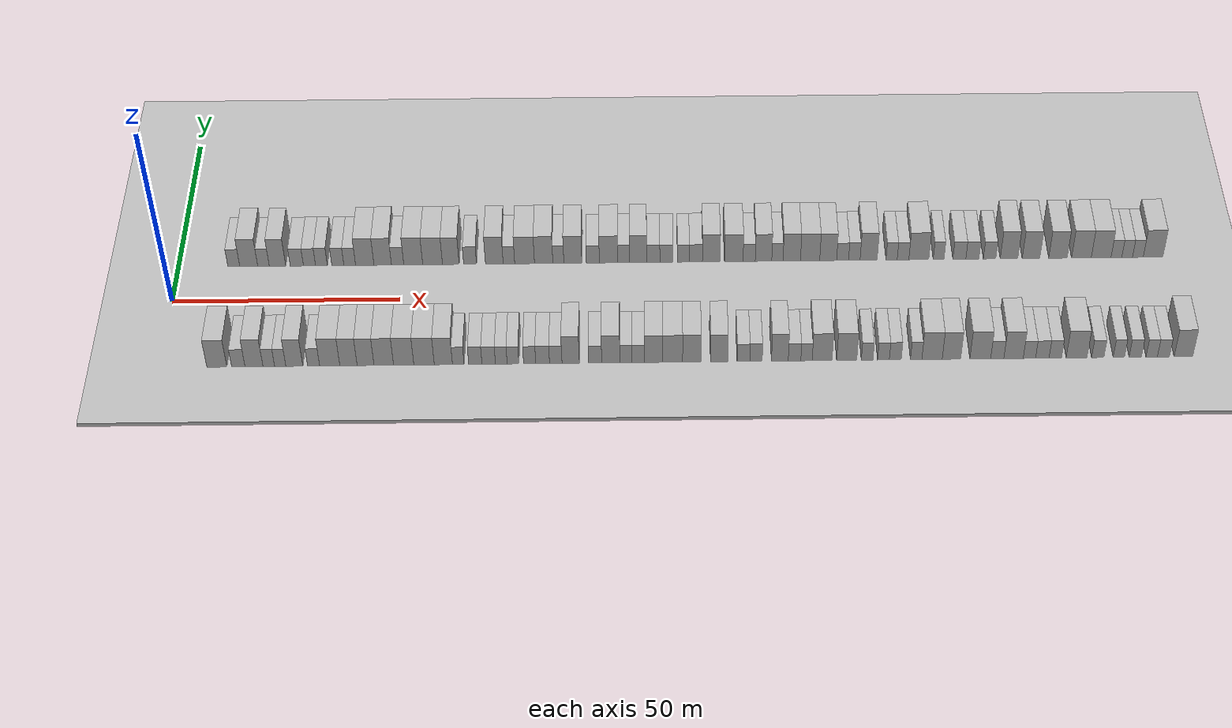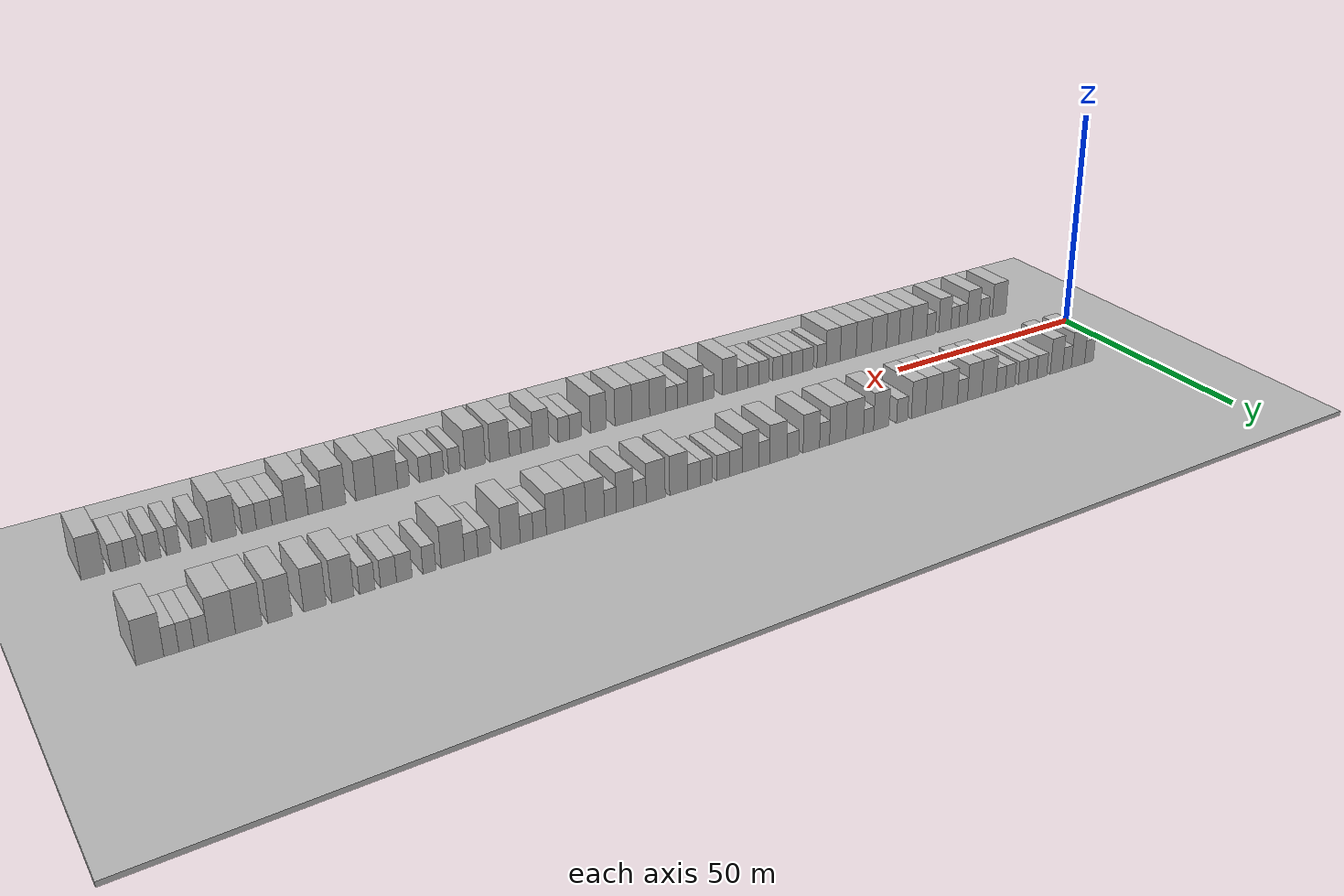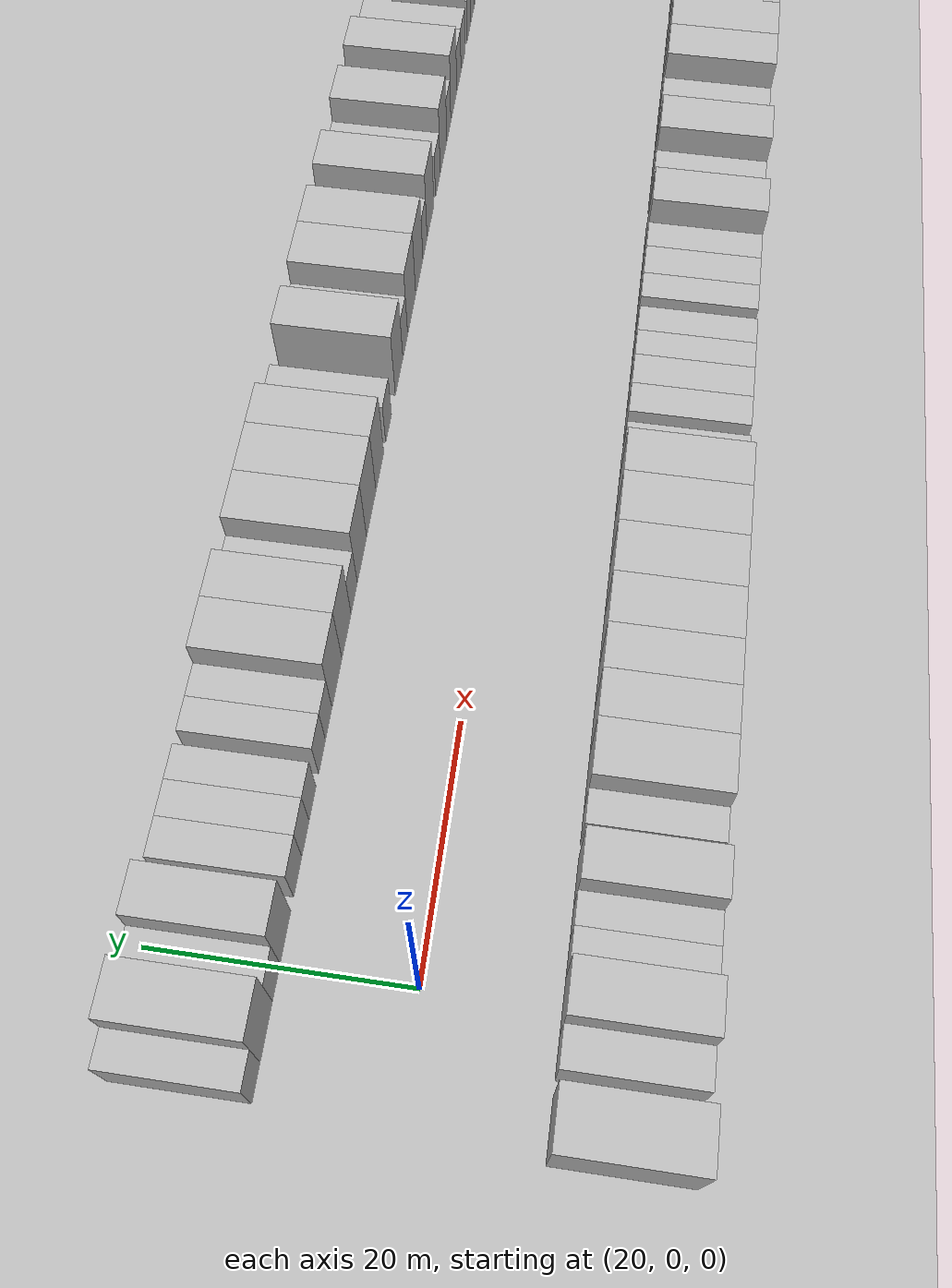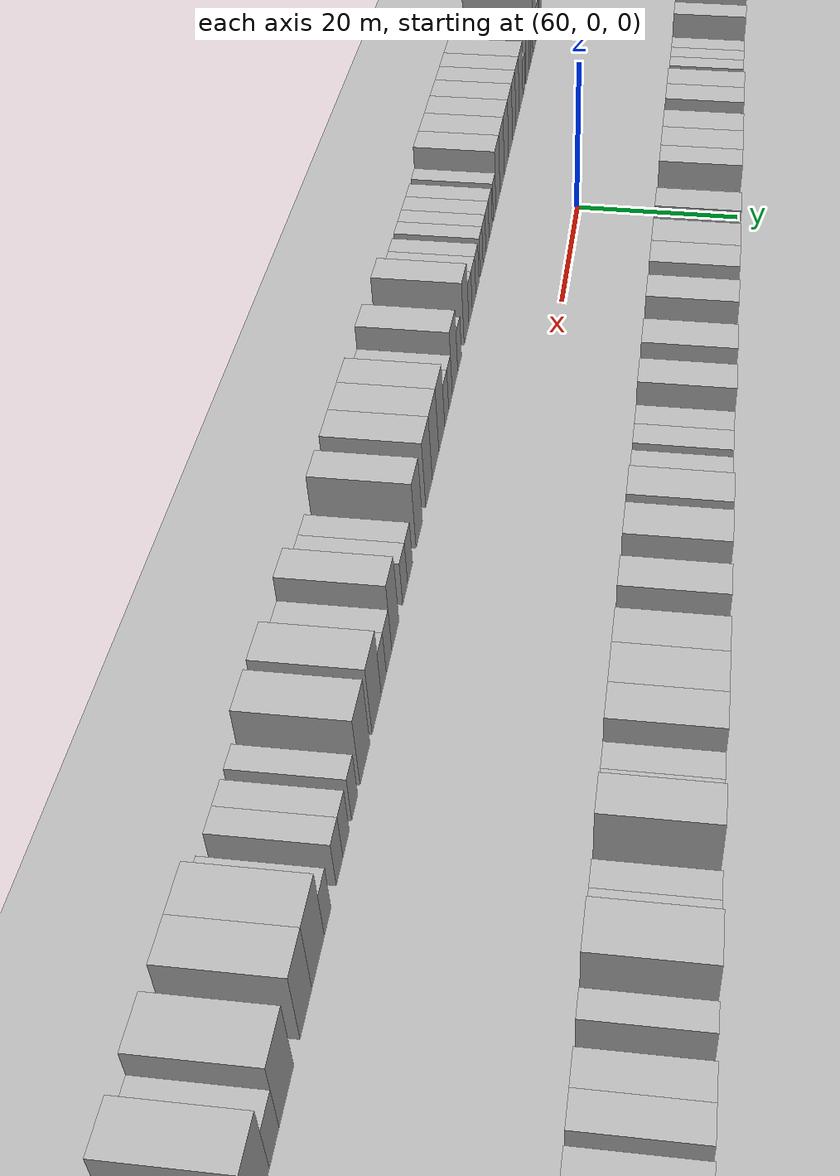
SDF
<?xml version="1.0" encoding="utf-8"?>

<sdf version="1.6">

   <world name="default">

      <gui fullscreen="0">

         <camera name="user_camera">

            <pose>-15 0 4.57585 0 0 0</pose>

            <view_controller>orbit</view_controller>

         </camera>

      </gui>

      <scene>

         <sky>

           <clouds>

             <speed>12</speed>

           </clouds>

         </sky>

         <ambient>0.4 0.4 0.4 1</ambient>

         <background>0.7 0.7 0.7 1</background>

         <shadows>1</shadows>

      </scene>

      <gravity>0 0 -9.8066</gravity>

      <magnetic_field>6e-06 2.3e-05 -4.2e-05</magnetic_field>

      <physics default="0" name="default_physics" type="ode">

         <ode>

            <solver>

               <type>quick</type>

               <iters>10</iters>

               <sor>1.0</sor>

               <use_dynamic_moi_rescaling>0</use_dynamic_moi_rescaling>

            </solver>

            <constraints>

               <cfm>0</cfm>

               <erp>0.2</erp>

               <contact_max_correcting_vel>100</contact_max_correcting_vel>

               <contact_surface_layer>0.001</contact_surface_layer>

            </constraints>

         </ode>

         <max_step_size>0.004</max_step_size>

         <real_time_factor>1</real_time_factor>

         <real_time_update_rate>250</real_time_update_rate>

      </physics>

      <light name="sun" type="directional">

         <cast_shadows>1</cast_shadows>

         <pose>0 0 10 0 0 0</pose>

         <diffuse>0.8 0.8 0.8 1</diffuse>

         <specular>0.2 0.2 0.2 1</specular>

         <attenuation>

            <range>1000</range>

            <constant>0.9</constant>

            <linear>0.01</linear>

            <quadratic>0.001</quadratic>

         </attenuation>

         <direction>-0.5 0.1 -0.9</direction>

      </light>

      <include>

         <name>ground_plane_1</name>

         <uri>model://HANNAS_ground_plane</uri>

         <pose>0 0 0  0 0 0</pose>

      </include>

      <include>

         <name>ground_plane_2</name>

         <uri>model://HANNAS_ground_plane</uri>

         <pose>100 0 0  0 0 0</pose>

      </include>

      <model name="building_1">

         <static>1</static>

         <pose frame="">12.3237 15.0000 0 0.000000 0.000000 1.570796</pose>

         <link name="link">

            <pose frame="">0 0 3.00 0 0 0</pose>

            <collision name="collision">

               <geometry>

                  <box>

                     <size>10.0000 2.6474 6.0000</size>

                  </box>

               </geometry>

               <max_contacts>10</max_contacts>

               <surface>

                  <contact>

                     <ode/>

                  </contact>

                  <bounce/>

                  <friction>

                     <torsional>

                        <ode/>

                     </torsional>

                     <ode/>

                  </friction>

               </surface>

            </collision>

            <visual name="visual">

               <cast_shadows>0</cast_shadows>

               <geometry>

                  <box>

                     <size>10.0000 2.6474 6.0000</size>

                  </box>

               </geometry>

               <material>

                  <script>

                     <uri>model://HANNAS_wall/materials/scripts</uri>

                     <uri>model://HANNAS_wall/materials/textures</uri>

                     <name>vrc/HANNAS_wall</name>

                  </script>

               </material>

            </visual>

            <self_collide>0</self_collide>

            <enable_wind>0</enable_wind>

            <kinematic>0</kinematic>

         </link>

      </model>

      <model name="building_2">

         <static>1</static>

         <pose frame="">15.6544 15.0000 0 0.000000 0.000000 1.570796</pose>

         <link name="link">

            <pose frame="">0 0 4.50 0 0 0</pose>

            <collision name="collision">

               <geometry>

                  <box>

                     <size>10.0000 4.0139 9.0000</size>

                  </box>

               </geometry>

               <max_contacts>10</max_contacts>

               <surface>

                  <contact>

                     <ode/>

                  </contact>

                  <bounce/>

                  <friction>

                     <torsional>

                        <ode/>

                     </torsional>

                     <ode/>

                  </friction>

               </surface>

            </collision>

            <visual name="visual">

               <cast_shadows>0</cast_shadows>

               <geometry>

                  <box>

                     <size>10.0000 4.0139 9.0000</size>

                  </box>

               </geometry>

               <material>

                  <script>

                     <uri>model://HANNAS_wall/materials/scripts</uri>

                     <uri>model://HANNAS_wall/materials/textures</uri>

                     <name>vrc/HANNAS_wall</name>

                  </script>

               </material>

            </visual>

            <self_collide>0</self_collide>

            <enable_wind>0</enable_wind>

            <kinematic>0</kinematic>

         </link>

      </model>

      <model name="building_3">

         <static>1</static>

         <pose frame="">18.9484 15.0000 0 0.000000 0.000000 1.570796</pose>

         <link name="link">

            <pose frame="">0 0 3.00 0 0 0</pose>

            <collision name="collision">

               <geometry>

                  <box>

                     <size>10.0000 2.5741 6.0000</size>

                  </box>

               </geometry>

               <max_contacts>10</max_contacts>

               <surface>

                  <contact>

                     <ode/>

                  </contact>

                  <bounce/>

                  <friction>

                     <torsional>

                        <ode/>

                     </torsional>

                     <ode/>

                  </friction>

               </surface>

            </collision>

            <visual name="visual">

               <cast_shadows>0</cast_shadows>

               <geometry>

                  <box>

                     <size>10.0000 2.5741 6.0000</size>

                  </box>

               </geometry>

               <material>

                  <script>

                     <uri>model://HANNAS_wall/materials/scripts</uri>

                     <uri>model://HANNAS_wall/materials/textures</uri>

                     <name>vrc/HANNAS_wall</name>

                  </script>

               </material>

            </visual>

            <self_collide>0</self_collide>

            <enable_wind>0</enable_wind>

            <kinematic>0</kinematic>

         </link>

      </model>

      <model name="building_4">

         <static>1</static>

         <pose frame="">22.0810 15.0000 0 0.000000 0.000000 1.570796</pose>

         <link name="link">

            <pose frame="">0 0 4.50 0 0 0</pose>

            <collision name="collision">

               <geometry>

                  <box>

                     <size>10.0000 3.6913 9.0000</size>

                  </box>

               </geometry>

               <max_contacts>10</max_contacts>

               <surface>

                  <contact>

                     <ode/>

                  </contact>

                  <bounce/>

                  <friction>

                     <torsional>

                        <ode/>

                     </torsional>

                     <ode/>

                  </friction>

               </surface>

            </collision>

            <visual name="visual">

               <cast_shadows>0</cast_shadows>

               <geometry>

                  <box>

                     <size>10.0000 3.6913 9.0000</size>

                  </box>

               </geometry>

               <material>

                  <script>

                     <uri>model://HANNAS_wall/materials/scripts</uri>

                     <uri>model://HANNAS_wall/materials/textures</uri>

                     <name>vrc/HANNAS_wall</name>

                  </script>

               </material>

            </visual>

            <self_collide>0</self_collide>

            <enable_wind>0</enable_wind>

            <kinematic>0</kinematic>

         </link>

      </model>

      <model name="building_5">

         <static>1</static>

         <pose frame="">26.3997 15.0000 0 0.000000 0.000000 1.570796</pose>

         <link name="link">

            <pose frame="">0 0 3.00 0 0 0</pose>

            <collision name="collision">

               <geometry>

                  <box>

                     <size>10.0000 2.9461 6.0000</size>

                  </box>

               </geometry>

               <max_contacts>10</max_contacts>

               <surface>

                  <contact>

                     <ode/>

                  </contact>

                  <bounce/>

                  <friction>

                     <torsional>

                        <ode/>

                     </torsional>

                     <ode/>

                  </friction>

               </surface>

            </collision>

            <visual name="visual">

               <cast_shadows>0</cast_shadows>

               <geometry>

                  <box>

                     <size>10.0000 2.9461 6.0000</size>

                  </box>

               </geometry>

               <material>

                  <script>

                     <uri>model://HANNAS_wall/materials/scripts</uri>

                     <uri>model://HANNAS_wall/materials/textures</uri>

                     <name>vrc/HANNAS_wall</name>

                  </script>

               </material>

            </visual>

            <self_collide>0</self_collide>

            <enable_wind>0</enable_wind>

            <kinematic>0</kinematic>

         </link>

      </model>

      <model name="building_6">

         <static>1</static>

         <pose frame="">29.2214 15.0000 0 0.000000 0.000000 1.570796</pose>

         <link name="link">

            <pose frame="">0 0 3.00 0 0 0</pose>

            <collision name="collision">

               <geometry>

                  <box>

                     <size>10.0000 2.6973 6.0000</size>

                  </box>

               </geometry>

               <max_contacts>10</max_contacts>

               <surface>

                  <contact>

                     <ode/>

                  </contact>

                  <bounce/>

                  <friction>

                     <torsional>

                        <ode/>

                     </torsional>

                     <ode/>

                  </friction>

               </surface>

            </collision>

            <visual name="visual">

               <cast_shadows>0</cast_shadows>

               <geometry>

                  <box>

                     <size>10.0000 2.6973 6.0000</size>

                  </box>

               </geometry>

               <material>

                  <script>

                     <uri>model://HANNAS_wall/materials/scripts</uri>

                     <uri>model://HANNAS_wall/materials/textures</uri>

                     <name>vrc/HANNAS_wall</name>

                  </script>

               </material>

            </visual>

            <self_collide>0</self_collide>

            <enable_wind>0</enable_wind>

            <kinematic>0</kinematic>

         </link>

      </model>

      <model name="building_7">

         <static>1</static>

         <pose frame="">31.8918 15.0000 0 0.000000 0.000000 1.570796</pose>

         <link name="link">

            <pose frame="">0 0 3.00 0 0 0</pose>

            <collision name="collision">

               <geometry>

                  <box>

                     <size>10.0000 2.6435 6.0000</size>

                  </box>

               </geometry>

               <max_contacts>10</max_contacts>

               <surface>

                  <contact>

                     <ode/>

                  </contact>

                  <bounce/>

                  <friction>

                     <torsional>

                        <ode/>

                     </torsional>

                     <ode/>

                  </friction>

               </surface>

            </collision>

            <visual name="visual">

               <cast_shadows>0</cast_shadows>

               <geometry>

                  <box>

                     <size>10.0000 2.6435 6.0000</size>

                  </box>

               </geometry>

               <material>

                  <script>

                     <uri>model://HANNAS_wall/materials/scripts</uri>

                     <uri>model://HANNAS_wall/materials/textures</uri>

                     <name>vrc/HANNAS_wall</name>

                  </script>

               </material>

            </visual>

            <self_collide>0</self_collide>

            <enable_wind>0</enable_wind>

            <kinematic>0</kinematic>

         </link>

      </model>

      <model name="building_8">

         <static>1</static>

         <pose frame="">35.5562 15.0000 0 0.000000 0.000000 1.570796</pose>

         <link name="link">

            <pose frame="">0 0 3.00 0 0 0</pose>

            <collision name="collision">

               <geometry>

                  <box>

                     <size>10.0000 2.6854 6.0000</size>

                  </box>

               </geometry>

               <max_contacts>10</max_contacts>

               <surface>

                  <contact>

                     <ode/>

                  </contact>

                  <bounce/>

                  <friction>

                     <torsional>

                        <ode/>

                     </torsional>

                     <ode/>

                  </friction>

               </surface>

            </collision>

            <visual name="visual">

               <cast_shadows>0</cast_shadows>

               <geometry>

                  <box>

                     <size>10.0000 2.6854 6.0000</size>

                  </box>

               </geometry>

               <material>

                  <script>

                     <uri>model://HANNAS_wall/materials/scripts</uri>

                     <uri>model://HANNAS_wall/materials/textures</uri>

                     <name>vrc/HANNAS_wall</name>

                  </script>

               </material>

            </visual>

            <self_collide>0</self_collide>

            <enable_wind>0</enable_wind>

            <kinematic>0</kinematic>

         </link>

      </model>

      <model name="building_9">

         <static>1</static>

         <pose frame="">38.2074 15.0000 0 0.000000 0.000000 1.570796</pose>

         <link name="link">

            <pose frame="">0 0 3.00 0 0 0</pose>

            <collision name="collision">

               <geometry>

                  <box>

                     <size>10.0000 2.6171 6.0000</size>

                  </box>

               </geometry>

               <max_contacts>10</max_contacts>

               <surface>

                  <contact>

                     <ode/>

                  </contact>

                  <bounce/>

                  <friction>

                     <torsional>

                        <ode/>

                     </torsional>

                     <ode/>

                  </friction>

               </surface>

            </collision>

            <visual name="visual">

               <cast_shadows>0</cast_shadows>

               <geometry>

                  <box>

                     <size>10.0000 2.6171 6.0000</size>

                  </box>

               </geometry>

               <material>

                  <script>

                     <uri>model://HANNAS_wall/materials/scripts</uri>

                     <uri>model://HANNAS_wall/materials/textures</uri>

                     <name>vrc/HANNAS_wall</name>

                  </script>

               </material>

            </visual>

            <self_collide>0</self_collide>

            <enable_wind>0</enable_wind>

            <kinematic>0</kinematic>

         </link>

      </model>

      <model name="building_10">

         <static>1</static>

         <pose frame="">41.5692 15.0000 0 0.000000 0.000000 1.570796</pose>

         <link name="link">

            <pose frame="">0 0 4.50 0 0 0</pose>

            <collision name="collision">

               <geometry>

                  <box>

                     <size>10.0000 4.1065 9.0000</size>

                  </box>

               </geometry>

               <max_contacts>10</max_contacts>

               <surface>

                  <contact>

                     <ode/>

                  </contact>

                  <bounce/>

                  <friction>

                     <torsional>

                        <ode/>

                     </torsional>

                     <ode/>

                  </friction>

               </surface>

            </collision>

            <visual name="visual">

               <cast_shadows>0</cast_shadows>

               <geometry>

                  <box>

                     <size>10.0000 4.1065 9.0000</size>

                  </box>

               </geometry>

               <material>

                  <script>

                     <uri>model://HANNAS_wall/materials/scripts</uri>

                     <uri>model://HANNAS_wall/materials/textures</uri>

                     <name>vrc/HANNAS_wall</name>

                  </script>

               </material>

            </visual>

            <self_collide>0</self_collide>

            <enable_wind>0</enable_wind>

            <kinematic>0</kinematic>

         </link>

      </model>

      <model name="building_11">

         <static>1</static>

         <pose frame="">45.5778 15.0000 0 0.000000 0.000000 1.570796</pose>

         <link name="link">

            <pose frame="">0 0 4.50 0 0 0</pose>

            <collision name="collision">

               <geometry>

                  <box>

                     <size>10.0000 3.9108 9.0000</size>

                  </box>

               </geometry>

               <max_contacts>10</max_contacts>

               <surface>

                  <contact>

                     <ode/>

                  </contact>

                  <bounce/>

                  <friction>

                     <torsional>

                        <ode/>

                     </torsional>

                     <ode/>

                  </friction>

               </surface>

            </collision>

            <visual name="visual">

               <cast_shadows>0</cast_shadows>

               <geometry>

                  <box>

                     <size>10.0000 3.9108 9.0000</size>

                  </box>

               </geometry>

               <material>

                  <script>

                     <uri>model://HANNAS_wall/materials/scripts</uri>

                     <uri>model://HANNAS_wall/materials/textures</uri>

                     <name>vrc/HANNAS_wall</name>

                  </script>

               </material>

            </visual>

            <self_collide>0</self_collide>

            <enable_wind>0</enable_wind>

            <kinematic>0</kinematic>

         </link>

      </model>

      <model name="building_12">

         <static>1</static>

         <pose frame="">48.9108 15.0000 0 0.000000 0.000000 1.570796</pose>

         <link name="link">

            <pose frame="">0 0 3.00 0 0 0</pose>

            <collision name="collision">

               <geometry>

                  <box>

                     <size>10.0000 2.7551 6.0000</size>

                  </box>

               </geometry>

               <max_contacts>10</max_contacts>

               <surface>

                  <contact>

                     <ode/>

                  </contact>

                  <bounce/>

                  <friction>

                     <torsional>

                        <ode/>

                     </torsional>

                     <ode/>

                  </friction>

               </surface>

            </collision>

            <visual name="visual">

               <cast_shadows>0</cast_shadows>

               <geometry>

                  <box>

                     <size>10.0000 2.7551 6.0000</size>

                  </box>

               </geometry>

               <material>

                  <script>

                     <uri>model://HANNAS_wall/materials/scripts</uri>

                     <uri>model://HANNAS_wall/materials/textures</uri>

                     <name>vrc/HANNAS_wall</name>

                  </script>

               </material>

            </visual>

            <self_collide>0</self_collide>

            <enable_wind>0</enable_wind>

            <kinematic>0</kinematic>

         </link>

      </model>

      <model name="building_13">

         <static>1</static>

         <pose frame="">52.4000 15.0000 0 0.000000 0.000000 1.570796</pose>

         <link name="link">

            <pose frame="">0 0 4.50 0 0 0</pose>

            <collision name="collision">

               <geometry>

                  <box>

                     <size>10.0000 4.2232 9.0000</size>

                  </box>

               </geometry>

               <max_contacts>10</max_contacts>

               <surface>

                  <contact>

                     <ode/>

                  </contact>

                  <bounce/>

                  <friction>

                     <torsional>

                        <ode/>

                     </torsional>

                     <ode/>

                  </friction>

               </surface>

            </collision>

            <visual name="visual">

               <cast_shadows>0</cast_shadows>

               <geometry>

                  <box>

                     <size>10.0000 4.2232 9.0000</size>

                  </box>

               </geometry>

               <material>

                  <script>

                     <uri>model://HANNAS_wall/materials/scripts</uri>

                     <uri>model://HANNAS_wall/materials/textures</uri>

                     <name>vrc/HANNAS_wall</name>

                  </script>

               </material>

            </visual>

            <self_collide>0</self_collide>

            <enable_wind>0</enable_wind>

            <kinematic>0</kinematic>

         </link>

      </model>

      <model name="building_14">

         <static>1</static>

         <pose frame="">56.7198 15.0000 0 0.000000 0.000000 1.570796</pose>

         <link name="link">

            <pose frame="">0 0 4.50 0 0 0</pose>

            <collision name="collision">

               <geometry>

                  <box>

                     <size>10.0000 4.4164 9.0000</size>

                  </box>

               </geometry>

               <max_contacts>10</max_contacts>

               <surface>

                  <contact>

                     <ode/>

                  </contact>

                  <bounce/>

                  <friction>

                     <torsional>

                        <ode/>

                     </torsional>

                     <ode/>

                  </friction>

               </surface>

            </collision>

            <visual name="visual">

               <cast_shadows>0</cast_shadows>

               <geometry>

                  <box>

                     <size>10.0000 4.4164 9.0000</size>

                  </box>

               </geometry>

               <material>

                  <script>

                     <uri>model://HANNAS_wall/materials/scripts</uri>

                     <uri>model://HANNAS_wall/materials/textures</uri>

                     <name>vrc/HANNAS_wall</name>

                  </script>

               </material>

            </visual>

            <self_collide>0</self_collide>

            <enable_wind>0</enable_wind>

            <kinematic>0</kinematic>

         </link>

      </model>

      <model name="building_15">

         <static>1</static>

         <pose frame="">60.7979 15.0000 0 0.000000 0.000000 1.570796</pose>

         <link name="link">

            <pose frame="">0 0 4.50 0 0 0</pose>

            <collision name="collision">

               <geometry>

                  <box>

                     <size>10.0000 3.7398 9.0000</size>

                  </box>

               </geometry>

               <max_contacts>10</max_contacts>

               <surface>

                  <contact>

                     <ode/>

                  </contact>

                  <bounce/>

                  <friction>

                     <torsional>

                        <ode/>

                     </torsional>

                     <ode/>

                  </friction>

               </surface>

            </collision>

            <visual name="visual">

               <cast_shadows>0</cast_shadows>

               <geometry>

                  <box>

                     <size>10.0000 3.7398 9.0000</size>

                  </box>

               </geometry>

               <material>

                  <script>

                     <uri>model://HANNAS_wall/materials/scripts</uri>

                     <uri>model://HANNAS_wall/materials/textures</uri>

                     <name>vrc/HANNAS_wall</name>

                  </script>

               </material>

            </visual>

            <self_collide>0</self_collide>

            <enable_wind>0</enable_wind>

            <kinematic>0</kinematic>

         </link>

      </model>

      <model name="building_16">

         <static>1</static>

         <pose frame="">65.1097 15.0000 0 0.000000 0.000000 1.570796</pose>

         <link name="link">

            <pose frame="">0 0 3.00 0 0 0</pose>

            <collision name="collision">

               <geometry>

                  <box>

                     <size>10.0000 2.8838 6.0000</size>

                  </box>

               </geometry>

               <max_contacts>10</max_contacts>

               <surface>

                  <contact>

                     <ode/>

                  </contact>

                  <bounce/>

                  <friction>

                     <torsional>

                        <ode/>

                     </torsional>

                     <ode/>

                  </friction>

               </surface>

            </collision>

            <visual name="visual">

               <cast_shadows>0</cast_shadows>

               <geometry>

                  <box>

                     <size>10.0000 2.8838 6.0000</size>

                  </box>

               </geometry>

               <material>

                  <script>

                     <uri>model://HANNAS_wall/materials/scripts</uri>

                     <uri>model://HANNAS_wall/materials/textures</uri>

                     <name>vrc/HANNAS_wall</name>

                  </script>

               </material>

            </visual>

            <self_collide>0</self_collide>

            <enable_wind>0</enable_wind>

            <kinematic>0</kinematic>

         </link>

      </model>

      <model name="building_17">

         <static>1</static>

         <pose frame="">70.5278 15.0000 0 0.000000 0.000000 1.570796</pose>

         <link name="link">

            <pose frame="">0 0 4.50 0 0 0</pose>

            <collision name="collision">

               <geometry>

                  <box>

                     <size>10.0000 3.9525 9.0000</size>

                  </box>

               </geometry>

               <max_contacts>10</max_contacts>

               <surface>

                  <contact>

                     <ode/>

                  </contact>

                  <bounce/>

                  <friction>

                     <torsional>

                        <ode/>

                     </torsional>

                     <ode/>

                  </friction>

               </surface>

            </collision>

            <visual name="visual">

               <cast_shadows>0</cast_shadows>

               <geometry>

                  <box>

                     <size>10.0000 3.9525 9.0000</size>

                  </box>

               </geometry>

               <material>

                  <script>

                     <uri>model://HANNAS_wall/materials/scripts</uri>

                     <uri>model://HANNAS_wall/materials/textures</uri>

                     <name>vrc/HANNAS_wall</name>

                  </script>

               </material>

            </visual>

            <self_collide>0</self_collide>

            <enable_wind>0</enable_wind>

            <kinematic>0</kinematic>

         </link>

      </model>

      <model name="building_18">

         <static>1</static>

         <pose frame="">73.7992 15.0000 0 0.000000 0.000000 1.570796</pose>

         <link name="link">

            <pose frame="">0 0 3.00 0 0 0</pose>

            <collision name="collision">

               <geometry>

                  <box>

                     <size>10.0000 2.5903 6.0000</size>

                  </box>

               </geometry>

               <max_contacts>10</max_contacts>

               <surface>

                  <contact>

                     <ode/>

                  </contact>

                  <bounce/>

                  <friction>

                     <torsional>

                        <ode/>

                     </torsional>

                     <ode/>

                  </friction>

               </surface>

            </collision>

            <visual name="visual">

               <cast_shadows>0</cast_shadows>

               <geometry>

                  <box>

                     <size>10.0000 2.5903 6.0000</size>

                  </box>

               </geometry>

               <material>

                  <script>

                     <uri>model://HANNAS_wall/materials/scripts</uri>

                     <uri>model://HANNAS_wall/materials/textures</uri>

                     <name>vrc/HANNAS_wall</name>

                  </script>

               </material>

            </visual>

            <self_collide>0</self_collide>

            <enable_wind>0</enable_wind>

            <kinematic>0</kinematic>

         </link>

      </model>

      <model name="building_19">

         <static>1</static>

         <pose frame="">77.3071 15.0000 0 0.000000 0.000000 1.570796</pose>

         <link name="link">

            <pose frame="">0 0 4.50 0 0 0</pose>

            <collision name="collision">

               <geometry>

                  <box>

                     <size>10.0000 4.4255 9.0000</size>

                  </box>

               </geometry>

               <max_contacts>10</max_contacts>

               <surface>

                  <contact>

                     <ode/>

                  </contact>

                  <bounce/>

                  <friction>

                     <torsional>

                        <ode/>

                     </torsional>

                     <ode/>

                  </friction>

               </surface>

            </collision>

            <visual name="visual">

               <cast_shadows>0</cast_shadows>

               <geometry>

                  <box>

                     <size>10.0000 4.4255 9.0000</size>

                  </box>

               </geometry>

               <material>

                  <script>

                     <uri>model://HANNAS_wall/materials/scripts</uri>

                     <uri>model://HANNAS_wall/materials/textures</uri>

                     <name>vrc/HANNAS_wall</name>

                  </script>

               </material>

            </visual>

            <self_collide>0</self_collide>

            <enable_wind>0</enable_wind>

            <kinematic>0</kinematic>

         </link>

      </model>

      <model name="building_20">

         <static>1</static>

         <pose frame="">81.5744 15.0000 0 0.000000 0.000000 1.570796</pose>

         <link name="link">

            <pose frame="">0 0 4.50 0 0 0</pose>

            <collision name="collision">

               <geometry>

                  <box>

                     <size>10.0000 4.1091 9.0000</size>

                  </box>

               </geometry>

               <max_contacts>10</max_contacts>

               <surface>

                  <contact>

                     <ode/>

                  </contact>

                  <bounce/>

                  <friction>

                     <torsional>

                        <ode/>

                     </torsional>

                     <ode/>

                  </friction>

               </surface>

            </collision>

            <visual name="visual">

               <cast_shadows>0</cast_shadows>

               <geometry>

                  <box>

                     <size>10.0000 4.1091 9.0000</size>

                  </box>

               </geometry>

               <material>

                  <script>

                     <uri>model://HANNAS_wall/materials/scripts</uri>

                     <uri>model://HANNAS_wall/materials/textures</uri>

                     <name>vrc/HANNAS_wall</name>

                  </script>

               </material>

            </visual>

            <self_collide>0</self_collide>

            <enable_wind>0</enable_wind>

            <kinematic>0</kinematic>

         </link>

      </model>

      <model name="building_21">

         <static>1</static>

         <pose frame="">84.8576 15.0000 0 0.000000 0.000000 1.570796</pose>

         <link name="link">

            <pose frame="">0 0 3.00 0 0 0</pose>

            <collision name="collision">

               <geometry>

                  <box>

                     <size>10.0000 2.4574 6.0000</size>

                  </box>

               </geometry>

               <max_contacts>10</max_contacts>

               <surface>

                  <contact>

                     <ode/>

                  </contact>

                  <bounce/>

                  <friction>

                     <torsional>

                        <ode/>

                     </torsional>

                     <ode/>

                  </friction>

               </surface>

            </collision>

            <visual name="visual">

               <cast_shadows>0</cast_shadows>

               <geometry>

                  <box>

                     <size>10.0000 2.4574 6.0000</size>

                  </box>

               </geometry>

               <material>

                  <script>

                     <uri>model://HANNAS_wall/materials/scripts</uri>

                     <uri>model://HANNAS_wall/materials/textures</uri>

                     <name>vrc/HANNAS_wall</name>

                  </script>

               </material>

            </visual>

            <self_collide>0</self_collide>

            <enable_wind>0</enable_wind>

            <kinematic>0</kinematic>

         </link>

      </model>

      <model name="building_22">

         <static>1</static>

         <pose frame="">88.1054 15.0000 0 0.000000 0.000000 1.570796</pose>

         <link name="link">

            <pose frame="">0 0 4.50 0 0 0</pose>

            <collision name="collision">

               <geometry>

                  <box>

                     <size>10.0000 4.0382 9.0000</size>

                  </box>

               </geometry>

               <max_contacts>10</max_contacts>

               <surface>

                  <contact>

                     <ode/>

                  </contact>

                  <bounce/>

                  <friction>

                     <torsional>

                        <ode/>

                     </torsional>

                     <ode/>

                  </friction>

               </surface>

            </collision>

            <visual name="visual">

               <cast_shadows>0</cast_shadows>

               <geometry>

                  <box>

                     <size>10.0000 4.0382 9.0000</size>

                  </box>

               </geometry>

               <material>

                  <script>

                     <uri>model://HANNAS_wall/materials/scripts</uri>

                     <uri>model://HANNAS_wall/materials/textures</uri>

                     <name>vrc/HANNAS_wall</name>

                  </script>

               </material>

            </visual>

            <self_collide>0</self_collide>

            <enable_wind>0</enable_wind>

            <kinematic>0</kinematic>

         </link>

      </model>

      <model name="building_23">

         <static>1</static>

         <pose frame="">92.5916 15.0000 0 0.000000 0.000000 1.570796</pose>

         <link name="link">

            <pose frame="">0 0 3.00 0 0 0</pose>

            <collision name="collision">

               <geometry>

                  <box>

                     <size>10.0000 2.9342 6.0000</size>

                  </box>

               </geometry>

               <max_contacts>10</max_contacts>

               <surface>

                  <contact>

                     <ode/>

                  </contact>

                  <bounce/>

                  <friction>

                     <torsional>

                        <ode/>

                     </torsional>

                     <ode/>

                  </friction>

               </surface>

            </collision>

            <visual name="visual">

               <cast_shadows>0</cast_shadows>

               <geometry>

                  <box>

                     <size>10.0000 2.9342 6.0000</size>

                  </box>

               </geometry>

               <material>

                  <script>

                     <uri>model://HANNAS_wall/materials/scripts</uri>

                     <uri>model://HANNAS_wall/materials/textures</uri>

                     <name>vrc/HANNAS_wall</name>

                  </script>

               </material>

            </visual>

            <self_collide>0</self_collide>

            <enable_wind>0</enable_wind>

            <kinematic>0</kinematic>

         </link>

      </model>

      <model name="building_24">

         <static>1</static>

         <pose frame="">96.1244 15.0000 0 0.000000 0.000000 1.570796</pose>

         <link name="link">

            <pose frame="">0 0 4.50 0 0 0</pose>

            <collision name="collision">

               <geometry>

                  <box>

                     <size>10.0000 4.1314 9.0000</size>

                  </box>

               </geometry>

               <max_contacts>10</max_contacts>

               <surface>

                  <contact>

                     <ode/>

                  </contact>

                  <bounce/>

                  <friction>

                     <torsional>

                        <ode/>

                     </torsional>

                     <ode/>

                  </friction>

               </surface>

            </collision>

            <visual name="visual">

               <cast_shadows>0</cast_shadows>

               <geometry>

                  <box>

                     <size>10.0000 4.1314 9.0000</size>

                  </box>

               </geometry>

               <material>

                  <script>

                     <uri>model://HANNAS_wall/materials/scripts</uri>

                     <uri>model://HANNAS_wall/materials/textures</uri>

                     <name>vrc/HANNAS_wall</name>

                  </script>

               </material>

            </visual>

            <self_collide>0</self_collide>

            <enable_wind>0</enable_wind>

            <kinematic>0</kinematic>

         </link>

      </model>

      <model name="building_25">

         <static>1</static>

         <pose frame="">99.4918 15.0000 0 0.000000 0.000000 1.570796</pose>

         <link name="link">

            <pose frame="">0 0 3.00 0 0 0</pose>

            <collision name="collision">

               <geometry>

                  <box>

                     <size>10.0000 2.6035 6.0000</size>

                  </box>

               </geometry>

               <max_contacts>10</max_contacts>

               <surface>

                  <contact>

                     <ode/>

                  </contact>

                  <bounce/>

                  <friction>

                     <torsional>

                        <ode/>

                     </torsional>

                     <ode/>

                  </friction>

               </surface>

            </collision>

            <visual name="visual">

               <cast_shadows>0</cast_shadows>

               <geometry>

                  <box>

                     <size>10.0000 2.6035 6.0000</size>

                  </box>

               </geometry>

               <material>

                  <script>

                     <uri>model://HANNAS_wall/materials/scripts</uri>

                     <uri>model://HANNAS_wall/materials/textures</uri>

                     <name>vrc/HANNAS_wall</name>

                  </script>

               </material>

            </visual>

            <self_collide>0</self_collide>

            <enable_wind>0</enable_wind>

            <kinematic>0</kinematic>

         </link>

      </model>

      <model name="building_26">

         <static>1</static>

         <pose frame="">102.7264 15.0000 0 0.000000 0.000000 1.570796</pose>

         <link name="link">

            <pose frame="">0 0 4.50 0 0 0</pose>

            <collision name="collision">

               <geometry>

                  <box>

                     <size>10.0000 3.8657 9.0000</size>

                  </box>

               </geometry>

               <max_contacts>10</max_contacts>

               <surface>

                  <contact>

                     <ode/>

                  </contact>

                  <bounce/>

                  <friction>

                     <torsional>

                        <ode/>

                     </torsional>

                     <ode/>

                  </friction>

               </surface>

            </collision>

            <visual name="visual">

               <cast_shadows>0</cast_shadows>

               <geometry>

                  <box>

                     <size>10.0000 3.8657 9.0000</size>

                  </box>

               </geometry>

               <material>

                  <script>

                     <uri>model://HANNAS_wall/materials/scripts</uri>

                     <uri>model://HANNAS_wall/materials/textures</uri>

                     <name>vrc/HANNAS_wall</name>

                  </script>

               </material>

            </visual>

            <self_collide>0</self_collide>

            <enable_wind>0</enable_wind>

            <kinematic>0</kinematic>

         </link>

      </model>

      <model name="building_27">

         <static>1</static>

         <pose frame="">106.1207 15.0000 0 0.000000 0.000000 1.570796</pose>

         <link name="link">

            <pose frame="">0 0 3.00 0 0 0</pose>

            <collision name="collision">

               <geometry>

                  <box>

                     <size>10.0000 2.9230 6.0000</size>

                  </box>

               </geometry>

               <max_contacts>10</max_contacts>

               <surface>

                  <contact>

                     <ode/>

                  </contact>

                  <bounce/>

                  <friction>

                     <torsional>

                        <ode/>

                     </torsional>

                     <ode/>

                  </friction>

               </surface>

            </collision>

            <visual name="visual">

               <cast_shadows>0</cast_shadows>

               <geometry>

                  <box>

                     <size>10.0000 2.9230 6.0000</size>

                  </box>

               </geometry>

               <material>

                  <script>

                     <uri>model://HANNAS_wall/materials/scripts</uri>

                     <uri>model://HANNAS_wall/materials/textures</uri>

                     <name>vrc/HANNAS_wall</name>

                  </script>

               </material>

            </visual>

            <self_collide>0</self_collide>

            <enable_wind>0</enable_wind>

            <kinematic>0</kinematic>

         </link>

      </model>

      <model name="building_28">

         <static>1</static>

         <pose frame="">109.0614 15.0000 0 0.000000 0.000000 1.570796</pose>

         <link name="link">

            <pose frame="">0 0 3.00 0 0 0</pose>

            <collision name="collision">

               <geometry>

                  <box>

                     <size>10.0000 2.9583 6.0000</size>

                  </box>

               </geometry>

               <max_contacts>10</max_contacts>

               <surface>

                  <contact>

                     <ode/>

                  </contact>

                  <bounce/>

                  <friction>

                     <torsional>

                        <ode/>

                     </torsional>

                     <ode/>

                  </friction>

               </surface>

            </collision>

            <visual name="visual">

               <cast_shadows>0</cast_shadows>

               <geometry>

                  <box>

                     <size>10.0000 2.9583 6.0000</size>

                  </box>

               </geometry>

               <material>

                  <script>

                     <uri>model://HANNAS_wall/materials/scripts</uri>

                     <uri>model://HANNAS_wall/materials/textures</uri>

                     <name>vrc/HANNAS_wall</name>

                  </script>

               </material>

            </visual>

            <self_collide>0</self_collide>

            <enable_wind>0</enable_wind>

            <kinematic>0</kinematic>

         </link>

      </model>

      <model name="building_29">

         <static>1</static>

         <pose frame="">112.8695 15.0000 0 0.000000 0.000000 1.570796</pose>

         <link name="link">

            <pose frame="">0 0 3.00 0 0 0</pose>

            <collision name="collision">

               <geometry>

                  <box>

                     <size>10.0000 2.6580 6.0000</size>

                  </box>

               </geometry>

               <max_contacts>10</max_contacts>

               <surface>

                  <contact>

                     <ode/>

                  </contact>

                  <bounce/>

                  <friction>

                     <torsional>

                        <ode/>

                     </torsional>

                     <ode/>

                  </friction>

               </surface>

            </collision>

            <visual name="visual">

               <cast_shadows>0</cast_shadows>

               <geometry>

                  <box>

                     <size>10.0000 2.6580 6.0000</size>

                  </box>

               </geometry>

               <material>

                  <script>

                     <uri>model://HANNAS_wall/materials/scripts</uri>

                     <uri>model://HANNAS_wall/materials/textures</uri>

                     <name>vrc/HANNAS_wall</name>

                  </script>

               </material>

            </visual>

            <self_collide>0</self_collide>

            <enable_wind>0</enable_wind>

            <kinematic>0</kinematic>

         </link>

      </model>

      <model name="building_30">

         <static>1</static>

         <pose frame="">115.6552 15.0000 0 0.000000 0.000000 1.570796</pose>

         <link name="link">

            <pose frame="">0 0 3.00 0 0 0</pose>

            <collision name="collision">

               <geometry>

                  <box>

                     <size>10.0000 2.9134 6.0000</size>

                  </box>

               </geometry>

               <max_contacts>10</max_contacts>

               <surface>

                  <contact>

                     <ode/>

                  </contact>

                  <bounce/>

                  <friction>

                     <torsional>

                        <ode/>

                     </torsional>

                     <ode/>

                  </friction>

               </surface>

            </collision>

            <visual name="visual">

               <cast_shadows>0</cast_shadows>

               <geometry>

                  <box>

                     <size>10.0000 2.9134 6.0000</size>

                  </box>

               </geometry>

               <material>

                  <script>

                     <uri>model://HANNAS_wall/materials/scripts</uri>

                     <uri>model://HANNAS_wall/materials/textures</uri>

                     <name>vrc/HANNAS_wall</name>

                  </script>

               </material>

            </visual>

            <self_collide>0</self_collide>

            <enable_wind>0</enable_wind>

            <kinematic>0</kinematic>

         </link>

      </model>

      <model name="building_31">

         <static>1</static>

         <pose frame="">119.0930 15.0000 0 0.000000 0.000000 1.570796</pose>

         <link name="link">

            <pose frame="">0 0 4.50 0 0 0</pose>

            <collision name="collision">

               <geometry>

                  <box>

                     <size>10.0000 3.9621 9.0000</size>

                  </box>

               </geometry>

               <max_contacts>10</max_contacts>

               <surface>

                  <contact>

                     <ode/>

                  </contact>

                  <bounce/>

                  <friction>

                     <torsional>

                        <ode/>

                     </torsional>

                     <ode/>

                  </friction>

               </surface>

            </collision>

            <visual name="visual">

               <cast_shadows>0</cast_shadows>

               <geometry>

                  <box>

                     <size>10.0000 3.9621 9.0000</size>

                  </box>

               </geometry>

               <material>

                  <script>

                     <uri>model://HANNAS_wall/materials/scripts</uri>

                     <uri>model://HANNAS_wall/materials/textures</uri>

                     <name>vrc/HANNAS_wall</name>

                  </script>

               </material>

            </visual>

            <self_collide>0</self_collide>

            <enable_wind>0</enable_wind>

            <kinematic>0</kinematic>

         </link>

      </model>

      <model name="building_32">

         <static>1</static>

         <pose frame="">124.1526 15.0000 0 0.000000 0.000000 1.570796</pose>

         <link name="link">

            <pose frame="">0 0 4.50 0 0 0</pose>

            <collision name="collision">

               <geometry>

                  <box>

                     <size>10.0000 4.1572 9.0000</size>

                  </box>

               </geometry>

               <max_contacts>10</max_contacts>

               <surface>

                  <contact>

                     <ode/>

                  </contact>

                  <bounce/>

                  <friction>

                     <torsional>

                        <ode/>

                     </torsional>

                     <ode/>

                  </friction>

               </surface>

            </collision>

            <visual name="visual">

               <cast_shadows>0</cast_shadows>

               <geometry>

                  <box>

                     <size>10.0000 4.1572 9.0000</size>

                  </box>

               </geometry>

               <material>

                  <script>

                     <uri>model://HANNAS_wall/materials/scripts</uri>

                     <uri>model://HANNAS_wall/materials/textures</uri>

                     <name>vrc/HANNAS_wall</name>

                  </script>

               </material>

            </visual>

            <self_collide>0</self_collide>

            <enable_wind>0</enable_wind>

            <kinematic>0</kinematic>

         </link>

      </model>

      <model name="building_33">

         <static>1</static>

         <pose frame="">127.5959 15.0000 0 0.000000 0.000000 1.570796</pose>

         <link name="link">

            <pose frame="">0 0 3.00 0 0 0</pose>

            <collision name="collision">

               <geometry>

                  <box>

                     <size>10.0000 2.7294 6.0000</size>

                  </box>

               </geometry>

               <max_contacts>10</max_contacts>

               <surface>

                  <contact>

                     <ode/>

                  </contact>

                  <bounce/>

                  <friction>

                     <torsional>

                        <ode/>

                     </torsional>

                     <ode/>

                  </friction>

               </surface>

            </collision>

            <visual name="visual">

               <cast_shadows>0</cast_shadows>

               <geometry>

                  <box>

                     <size>10.0000 2.7294 6.0000</size>

                  </box>

               </geometry>

               <material>

                  <script>

                     <uri>model://HANNAS_wall/materials/scripts</uri>

                     <uri>model://HANNAS_wall/materials/textures</uri>

                     <name>vrc/HANNAS_wall</name>

                  </script>

               </material>

            </visual>

            <self_collide>0</self_collide>

            <enable_wind>0</enable_wind>

            <kinematic>0</kinematic>

         </link>

      </model>

      <model name="building_34">

         <static>1</static>

         <pose frame="">130.8069 15.0000 0 0.000000 0.000000 1.570796</pose>

         <link name="link">

            <pose frame="">0 0 4.50 0 0 0</pose>

            <collision name="collision">

               <geometry>

                  <box>

                     <size>10.0000 3.6927 9.0000</size>

                  </box>

               </geometry>

               <max_contacts>10</max_contacts>

               <surface>

                  <contact>

                     <ode/>

                  </contact>

                  <bounce/>

                  <friction>

                     <torsional>

                        <ode/>

                     </torsional>

                     <ode/>

                  </friction>

               </surface>

            </collision>

            <visual name="visual">

               <cast_shadows>0</cast_shadows>

               <geometry>

                  <box>

                     <size>10.0000 3.6927 9.0000</size>

                  </box>

               </geometry>

               <material>

                  <script>

                     <uri>model://HANNAS_wall/materials/scripts</uri>

                     <uri>model://HANNAS_wall/materials/textures</uri>

                     <name>vrc/HANNAS_wall</name>

                  </script>

               </material>

            </visual>

            <self_collide>0</self_collide>

            <enable_wind>0</enable_wind>

            <kinematic>0</kinematic>

         </link>

      </model>

      <model name="building_35">

         <static>1</static>

         <pose frame="">133.9190 15.0000 0 0.000000 0.000000 1.570796</pose>

         <link name="link">

            <pose frame="">0 0 3.00 0 0 0</pose>

            <collision name="collision">

               <geometry>

                  <box>

                     <size>10.0000 2.5314 6.0000</size>

                  </box>

               </geometry>

               <max_contacts>10</max_contacts>

               <surface>

                  <contact>

                     <ode/>

                  </contact>

                  <bounce/>

                  <friction>

                     <torsional>

                        <ode/>

                     </torsional>

                     <ode/>

                  </friction>

               </surface>

            </collision>

            <visual name="visual">

               <cast_shadows>0</cast_shadows>

               <geometry>

                  <box>

                     <size>10.0000 2.5314 6.0000</size>

                  </box>

               </geometry>

               <material>

                  <script>

                     <uri>model://HANNAS_wall/materials/scripts</uri>

                     <uri>model://HANNAS_wall/materials/textures</uri>

                     <name>vrc/HANNAS_wall</name>

                  </script>

               </material>

            </visual>

            <self_collide>0</self_collide>

            <enable_wind>0</enable_wind>

            <kinematic>0</kinematic>

         </link>

      </model>

      <model name="building_36">

         <static>1</static>

         <pose frame="">137.1407 15.0000 0 0.000000 0.000000 1.570796</pose>

         <link name="link">

            <pose frame="">0 0 4.50 0 0 0</pose>

            <collision name="collision">

               <geometry>

                  <box>

                     <size>10.0000 3.9121 9.0000</size>

                  </box>

               </geometry>

               <max_contacts>10</max_contacts>

               <surface>

                  <contact>

                     <ode/>

                  </contact>

                  <bounce/>

                  <friction>

                     <torsional>

                        <ode/>

                     </torsional>

                     <ode/>

                  </friction>

               </surface>

            </collision>

            <visual name="visual">

               <cast_shadows>0</cast_shadows>

               <geometry>

                  <box>

                     <size>10.0000 3.9121 9.0000</size>

                  </box>

               </geometry>

               <material>

                  <script>

                     <uri>model://HANNAS_wall/materials/scripts</uri>

                     <uri>model://HANNAS_wall/materials/textures</uri>

                     <name>vrc/HANNAS_wall</name>

                  </script>

               </material>

            </visual>

            <self_collide>0</self_collide>

            <enable_wind>0</enable_wind>

            <kinematic>0</kinematic>

         </link>

      </model>

      <model name="building_37">

         <static>1</static>

         <pose frame="">141.2572 15.0000 0 0.000000 0.000000 1.570796</pose>

         <link name="link">

            <pose frame="">0 0 4.50 0 0 0</pose>

            <collision name="collision">

               <geometry>

                  <box>

                     <size>10.0000 4.3211 9.0000</size>

                  </box>

               </geometry>

               <max_contacts>10</max_contacts>

               <surface>

                  <contact>

                     <ode/>

                  </contact>

                  <bounce/>

                  <friction>

                     <torsional>

                        <ode/>

                     </torsional>

                     <ode/>

                  </friction>

               </surface>

            </collision>

            <visual name="visual">

               <cast_shadows>0</cast_shadows>

               <geometry>

                  <box>

                     <size>10.0000 4.3211 9.0000</size>

                  </box>

               </geometry>

               <material>

                  <script>

                     <uri>model://HANNAS_wall/materials/scripts</uri>

                     <uri>model://HANNAS_wall/materials/textures</uri>

                     <name>vrc/HANNAS_wall</name>

                  </script>

               </material>

            </visual>

            <self_collide>0</self_collide>

            <enable_wind>0</enable_wind>

            <kinematic>0</kinematic>

         </link>

      </model>

      <model name="building_38">

         <static>1</static>

         <pose frame="">145.3111 15.0000 0 0.000000 0.000000 1.570796</pose>

         <link name="link">

            <pose frame="">0 0 4.50 0 0 0</pose>

            <collision name="collision">

               <geometry>

                  <box>

                     <size>10.0000 3.7867 9.0000</size>

                  </box>

               </geometry>

               <max_contacts>10</max_contacts>

               <surface>

                  <contact>

                     <ode/>

                  </contact>

                  <bounce/>

                  <friction>

                     <torsional>

                        <ode/>

                     </torsional>

                     <ode/>

                  </friction>

               </surface>

            </collision>

            <visual name="visual">

               <cast_shadows>0</cast_shadows>

               <geometry>

                  <box>

                     <size>10.0000 3.7867 9.0000</size>

                  </box>

               </geometry>

               <material>

                  <script>

                     <uri>model://HANNAS_wall/materials/scripts</uri>

                     <uri>model://HANNAS_wall/materials/textures</uri>

                     <name>vrc/HANNAS_wall</name>

                  </script>

               </material>

            </visual>

            <self_collide>0</self_collide>

            <enable_wind>0</enable_wind>

            <kinematic>0</kinematic>

         </link>

      </model>

      <model name="building_39">

         <static>1</static>

         <pose frame="">148.5455 15.0000 0 0.000000 0.000000 1.570796</pose>

         <link name="link">

            <pose frame="">0 0 3.00 0 0 0</pose>

            <collision name="collision">

               <geometry>

                  <box>

                     <size>10.0000 2.6821 6.0000</size>

                  </box>

               </geometry>

               <max_contacts>10</max_contacts>

               <surface>

                  <contact>

                     <ode/>

                  </contact>

                  <bounce/>

                  <friction>

                     <torsional>

                        <ode/>

                     </torsional>

                     <ode/>

                  </friction>

               </surface>

            </collision>

            <visual name="visual">

               <cast_shadows>0</cast_shadows>

               <geometry>

                  <box>

                     <size>10.0000 2.6821 6.0000</size>

                  </box>

               </geometry>

               <material>

                  <script>

                     <uri>model://HANNAS_wall/materials/scripts</uri>

                     <uri>model://HANNAS_wall/materials/textures</uri>

                     <name>vrc/HANNAS_wall</name>

                  </script>

               </material>

            </visual>

            <self_collide>0</self_collide>

            <enable_wind>0</enable_wind>

            <kinematic>0</kinematic>

         </link>

      </model>

      <model name="building_40">

         <static>1</static>

         <pose frame="">151.1820 15.0000 0 0.000000 0.000000 1.570796</pose>

         <link name="link">

            <pose frame="">0 0 3.00 0 0 0</pose>

            <collision name="collision">

               <geometry>

                  <box>

                     <size>10.0000 2.5909 6.0000</size>

                  </box>

               </geometry>

               <max_contacts>10</max_contacts>

               <surface>

                  <contact>

                     <ode/>

                  </contact>

                  <bounce/>

                  <friction>

                     <torsional>

                        <ode/>

                     </torsional>

                     <ode/>

                  </friction>

               </surface>

            </collision>

            <visual name="visual">

               <cast_shadows>0</cast_shadows>

               <geometry>

                  <box>

                     <size>10.0000 2.5909 6.0000</size>

                  </box>

               </geometry>

               <material>

                  <script>

                     <uri>model://HANNAS_wall/materials/scripts</uri>

                     <uri>model://HANNAS_wall/materials/textures</uri>

                     <name>vrc/HANNAS_wall</name>

                  </script>

               </material>

            </visual>

            <self_collide>0</self_collide>

            <enable_wind>0</enable_wind>

            <kinematic>0</kinematic>

         </link>

      </model>

      <model name="building_41">

         <static>1</static>

         <pose frame="">154.3863 15.0000 0 0.000000 0.000000 1.570796</pose>

         <link name="link">

            <pose frame="">0 0 4.50 0 0 0</pose>

            <collision name="collision">

               <geometry>

                  <box>

                     <size>10.0000 3.8178 9.0000</size>

                  </box>

               </geometry>

               <max_contacts>10</max_contacts>

               <surface>

                  <contact>

                     <ode/>

                  </contact>

                  <bounce/>

                  <friction>

                     <torsional>

                        <ode/>

                     </torsional>

                     <ode/>

                  </friction>

               </surface>

            </collision>

            <visual name="visual">

               <cast_shadows>0</cast_shadows>

               <geometry>

                  <box>

                     <size>10.0000 3.8178 9.0000</size>

                  </box>

               </geometry>

               <material>

                  <script>

                     <uri>model://HANNAS_wall/materials/scripts</uri>

                     <uri>model://HANNAS_wall/materials/textures</uri>

                     <name>vrc/HANNAS_wall</name>

                  </script>

               </material>

            </visual>

            <self_collide>0</self_collide>

            <enable_wind>0</enable_wind>

            <kinematic>0</kinematic>

         </link>

      </model>

      <model name="building_42">

         <static>1</static>

         <pose frame="">159.5500 15.0000 0 0.000000 0.000000 1.570796</pose>

         <link name="link">

            <pose frame="">0 0 3.00 0 0 0</pose>

            <collision name="collision">

               <geometry>

                  <box>

                     <size>10.0000 2.5095 6.0000</size>

                  </box>

               </geometry>

               <max_contacts>10</max_contacts>

               <surface>

                  <contact>

                     <ode/>

                  </contact>

                  <bounce/>

                  <friction>

                     <torsional>

                        <ode/>

                     </torsional>

                     <ode/>

                  </friction>

               </surface>

            </collision>

            <visual name="visual">

               <cast_shadows>0</cast_shadows>

               <geometry>

                  <box>

                     <size>10.0000 2.5095 6.0000</size>

                  </box>

               </geometry>

               <material>

                  <script>

                     <uri>model://HANNAS_wall/materials/scripts</uri>

                     <uri>model://HANNAS_wall/materials/textures</uri>

                     <name>vrc/HANNAS_wall</name>

                  </script>

               </material>

            </visual>

            <self_collide>0</self_collide>

            <enable_wind>0</enable_wind>

            <kinematic>0</kinematic>

         </link>

      </model>

      <model name="building_43">

         <static>1</static>

         <pose frame="">162.1150 15.0000 0 0.000000 0.000000 1.570796</pose>

         <link name="link">

            <pose frame="">0 0 3.00 0 0 0</pose>

            <collision name="collision">

               <geometry>

                  <box>

                     <size>10.0000 2.6204 6.0000</size>

                  </box>

               </geometry>

               <max_contacts>10</max_contacts>

               <surface>

                  <contact>

                     <ode/>

                  </contact>

                  <bounce/>

                  <friction>

                     <torsional>

                        <ode/>

                     </torsional>

                     <ode/>

                  </friction>

               </surface>

            </collision>

            <visual name="visual">

               <cast_shadows>0</cast_shadows>

               <geometry>

                  <box>

                     <size>10.0000 2.6204 6.0000</size>

                  </box>

               </geometry>

               <material>

                  <script>

                     <uri>model://HANNAS_wall/materials/scripts</uri>

                     <uri>model://HANNAS_wall/materials/textures</uri>

                     <name>vrc/HANNAS_wall</name>

                  </script>

               </material>

            </visual>

            <self_collide>0</self_collide>

            <enable_wind>0</enable_wind>

            <kinematic>0</kinematic>

         </link>

      </model>

      <model name="building_44">

         <static>1</static>

         <pose frame="">165.6594 15.0000 0 0.000000 0.000000 1.570796</pose>

         <link name="link">

            <pose frame="">0 0 4.50 0 0 0</pose>

            <collision name="collision">

               <geometry>

                  <box>

                     <size>10.0000 4.4684 9.0000</size>

                  </box>

               </geometry>

               <max_contacts>10</max_contacts>

               <surface>

                  <contact>

                     <ode/>

                  </contact>

                  <bounce/>

                  <friction>

                     <torsional>

                        <ode/>

                     </torsional>

                     <ode/>

                  </friction>

               </surface>

            </collision>

            <visual name="visual">

               <cast_shadows>0</cast_shadows>

               <geometry>

                  <box>

                     <size>10.0000 4.4684 9.0000</size>

                  </box>

               </geometry>

               <material>

                  <script>

                     <uri>model://HANNAS_wall/materials/scripts</uri>

                     <uri>model://HANNAS_wall/materials/textures</uri>

                     <name>vrc/HANNAS_wall</name>

                  </script>

               </material>

            </visual>

            <self_collide>0</self_collide>

            <enable_wind>0</enable_wind>

            <kinematic>0</kinematic>

         </link>

      </model>

      <model name="building_45">

         <static>1</static>

         <pose frame="">170.1038 15.0000 0 0.000000 0.000000 1.570796</pose>

         <link name="link">

            <pose frame="">0 0 3.00 0 0 0</pose>

            <collision name="collision">

               <geometry>

                  <box>

                     <size>10.0000 2.4204 6.0000</size>

                  </box>

               </geometry>

               <max_contacts>10</max_contacts>

               <surface>

                  <contact>

                     <ode/>

                  </contact>

                  <bounce/>

                  <friction>

                     <torsional>

                        <ode/>

                     </torsional>

                     <ode/>

                  </friction>

               </surface>

            </collision>

            <visual name="visual">

               <cast_shadows>0</cast_shadows>

               <geometry>

                  <box>

                     <size>10.0000 2.4204 6.0000</size>

                  </box>

               </geometry>

               <material>

                  <script>

                     <uri>model://HANNAS_wall/materials/scripts</uri>

                     <uri>model://HANNAS_wall/materials/textures</uri>

                     <name>vrc/HANNAS_wall</name>

                  </script>

               </material>

            </visual>

            <self_collide>0</self_collide>

            <enable_wind>0</enable_wind>

            <kinematic>0</kinematic>

         </link>

      </model>

      <model name="building_46">

         <static>1</static>

         <pose frame="">174.7673 15.0000 0 0.000000 0.000000 1.570796</pose>

         <link name="link">

            <pose frame="">0 0 3.00 0 0 0</pose>

            <collision name="collision">

               <geometry>

                  <box>

                     <size>10.0000 2.9066 6.0000</size>

                  </box>

               </geometry>

               <max_contacts>10</max_contacts>

               <surface>

                  <contact>

                     <ode/>

                  </contact>

                  <bounce/>

                  <friction>

                     <torsional>

                        <ode/>

                     </torsional>

                     <ode/>

                  </friction>

               </surface>

            </collision>

            <visual name="visual">

               <cast_shadows>0</cast_shadows>

               <geometry>

                  <box>

                     <size>10.0000 2.9066 6.0000</size>

                  </box>

               </geometry>

               <material>

                  <script>

                     <uri>model://HANNAS_wall/materials/scripts</uri>

                     <uri>model://HANNAS_wall/materials/textures</uri>

                     <name>vrc/HANNAS_wall</name>

                  </script>

               </material>

            </visual>

            <self_collide>0</self_collide>

            <enable_wind>0</enable_wind>

            <kinematic>0</kinematic>

         </link>

      </model>

      <model name="building_47">

         <static>1</static>

         <pose frame="">177.6863 15.0000 0 0.000000 0.000000 1.570796</pose>

         <link name="link">

            <pose frame="">0 0 3.00 0 0 0</pose>

            <collision name="collision">

               <geometry>

                  <box>

                     <size>10.0000 2.9313 6.0000</size>

                  </box>

               </geometry>

               <max_contacts>10</max_contacts>

               <surface>

                  <contact>

                     <ode/>

                  </contact>

                  <bounce/>

                  <friction>

                     <torsional>

                        <ode/>

                     </torsional>

                     <ode/>

                  </friction>

               </surface>

            </collision>

            <visual name="visual">

               <cast_shadows>0</cast_shadows>

               <geometry>

                  <box>

                     <size>10.0000 2.9313 6.0000</size>

                  </box>

               </geometry>

               <material>

                  <script>

                     <uri>model://HANNAS_wall/materials/scripts</uri>

                     <uri>model://HANNAS_wall/materials/textures</uri>

                     <name>vrc/HANNAS_wall</name>

                  </script>

               </material>

            </visual>

            <self_collide>0</self_collide>

            <enable_wind>0</enable_wind>

            <kinematic>0</kinematic>

         </link>

      </model>

      <model name="building_48">

         <static>1</static>

         <pose frame="">181.5532 15.0000 0 0.000000 0.000000 1.570796</pose>

         <link name="link">

            <pose frame="">0 0 3.00 0 0 0</pose>

            <collision name="collision">

               <geometry>

                  <box>

                     <size>10.0000 2.8025 6.0000</size>

                  </box>

               </geometry>

               <max_contacts>10</max_contacts>

               <surface>

                  <contact>

                     <ode/>

                  </contact>

                  <bounce/>

                  <friction>

                     <torsional>

                        <ode/>

                     </torsional>

                     <ode/>

                  </friction>

               </surface>

            </collision>

            <visual name="visual">

               <cast_shadows>0</cast_shadows>

               <geometry>

                  <box>

                     <size>10.0000 2.8025 6.0000</size>

                  </box>

               </geometry>

               <material>

                  <script>

                     <uri>model://HANNAS_wall/materials/scripts</uri>

                     <uri>model://HANNAS_wall/materials/textures</uri>

                     <name>vrc/HANNAS_wall</name>

                  </script>

               </material>

            </visual>

            <self_collide>0</self_collide>

            <enable_wind>0</enable_wind>

            <kinematic>0</kinematic>

         </link>

      </model>

      <model name="building_49">

         <static>1</static>

         <pose frame="">185.9270 15.0000 0 0.000000 0.000000 1.570796</pose>

         <link name="link">

            <pose frame="">0 0 4.50 0 0 0</pose>

            <collision name="collision">

               <geometry>

                  <box>

                     <size>10.0000 3.9450 9.0000</size>

                  </box>

               </geometry>

               <max_contacts>10</max_contacts>

               <surface>

                  <contact>

                     <ode/>

                  </contact>

                  <bounce/>

                  <friction>

                     <torsional>

                        <ode/>

                     </torsional>

                     <ode/>

                  </friction>

               </surface>

            </collision>

            <visual name="visual">

               <cast_shadows>0</cast_shadows>

               <geometry>

                  <box>

                     <size>10.0000 3.9450 9.0000</size>

                  </box>

               </geometry>

               <material>

                  <script>

                     <uri>model://HANNAS_wall/materials/scripts</uri>

                     <uri>model://HANNAS_wall/materials/textures</uri>

                     <name>vrc/HANNAS_wall</name>

                  </script>

               </material>

            </visual>

            <self_collide>0</self_collide>

            <enable_wind>0</enable_wind>

            <kinematic>0</kinematic>

         </link>

      </model>

      <model name="building_50">

         <static>1</static>

         <pose frame="">190.8726 15.0000 0 0.000000 0.000000 1.570796</pose>

         <link name="link">

            <pose frame="">0 0 4.50 0 0 0</pose>

            <collision name="collision">

               <geometry>

                  <box>

                     <size>10.0000 3.9462 9.0000</size>

                  </box>

               </geometry>

               <max_contacts>10</max_contacts>

               <surface>

                  <contact>

                     <ode/>

                  </contact>

                  <bounce/>

                  <friction>

                     <torsional>

                        <ode/>

                     </torsional>

                     <ode/>

                  </friction>

               </surface>

            </collision>

            <visual name="visual">

               <cast_shadows>0</cast_shadows>

               <geometry>

                  <box>

                     <size>10.0000 3.9462 9.0000</size>

                  </box>

               </geometry>

               <material>

                  <script>

                     <uri>model://HANNAS_wall/materials/scripts</uri>

                     <uri>model://HANNAS_wall/materials/textures</uri>

                     <name>vrc/HANNAS_wall</name>

                  </script>

               </material>

            </visual>

            <self_collide>0</self_collide>

            <enable_wind>0</enable_wind>

            <kinematic>0</kinematic>

         </link>

      </model>

      <model name="building_51">

         <static>1</static>

         <pose frame="">196.9149 15.0000 0 0.000000 0.000000 1.570796</pose>

         <link name="link">

            <pose frame="">0 0 4.50 0 0 0</pose>

            <collision name="collision">

               <geometry>

                  <box>

                     <size>10.0000 4.1385 9.0000</size>

                  </box>

               </geometry>

               <max_contacts>10</max_contacts>

               <surface>

                  <contact>

                     <ode/>

                  </contact>

                  <bounce/>

                  <friction>

                     <torsional>

                        <ode/>

                     </torsional>

                     <ode/>

                  </friction>

               </surface>

            </collision>

            <visual name="visual">

               <cast_shadows>0</cast_shadows>

               <geometry>

                  <box>

                     <size>10.0000 4.1385 9.0000</size>

                  </box>

               </geometry>

               <material>

                  <script>

                     <uri>model://HANNAS_wall/materials/scripts</uri>

                     <uri>model://HANNAS_wall/materials/textures</uri>

                     <name>vrc/HANNAS_wall</name>

                  </script>

               </material>

            </visual>

            <self_collide>0</self_collide>

            <enable_wind>0</enable_wind>

            <kinematic>0</kinematic>

         </link>

      </model>

      <model name="building_52">

         <static>1</static>

         <pose frame="">202.2018 15.0000 0 0.000000 0.000000 1.570796</pose>

         <link name="link">

            <pose frame="">0 0 4.50 0 0 0</pose>

            <collision name="collision">

               <geometry>

                  <box>

                     <size>10.0000 4.4352 9.0000</size>

                  </box>

               </geometry>

               <max_contacts>10</max_contacts>

               <surface>

                  <contact>

                     <ode/>

                  </contact>

                  <bounce/>

                  <friction>

                     <torsional>

                        <ode/>

                     </torsional>

                     <ode/>

                  </friction>

               </surface>

            </collision>

            <visual name="visual">

               <cast_shadows>0</cast_shadows>

               <geometry>

                  <box>

                     <size>10.0000 4.4352 9.0000</size>

                  </box>

               </geometry>

               <material>

                  <script>

                     <uri>model://HANNAS_wall/materials/scripts</uri>

                     <uri>model://HANNAS_wall/materials/textures</uri>

                     <name>vrc/HANNAS_wall</name>

                  </script>

               </material>

            </visual>

            <self_collide>0</self_collide>

            <enable_wind>0</enable_wind>

            <kinematic>0</kinematic>

         </link>

      </model>

      <model name="building_53">

         <static>1</static>

         <pose frame="">206.6403 15.0000 0 0.000000 0.000000 1.570796</pose>

         <link name="link">

            <pose frame="">0 0 4.50 0 0 0</pose>

            <collision name="collision">

               <geometry>

                  <box>

                     <size>10.0000 4.4420 9.0000</size>

                  </box>

               </geometry>

               <max_contacts>10</max_contacts>

               <surface>

                  <contact>

                     <ode/>

                  </contact>

                  <bounce/>

                  <friction>

                     <torsional>

                        <ode/>

                     </torsional>

                     <ode/>

                  </friction>

               </surface>

            </collision>

            <visual name="visual">

               <cast_shadows>0</cast_shadows>

               <geometry>

                  <box>

                     <size>10.0000 4.4420 9.0000</size>

                  </box>

               </geometry>

               <material>

                  <script>

                     <uri>model://HANNAS_wall/materials/scripts</uri>

                     <uri>model://HANNAS_wall/materials/textures</uri>

                     <name>vrc/HANNAS_wall</name>

                  </script>

               </material>

            </visual>

            <self_collide>0</self_collide>

            <enable_wind>0</enable_wind>

            <kinematic>0</kinematic>

         </link>

      </model>

      <model name="building_54">

         <static>1</static>

         <pose frame="">210.0744 15.0000 0 0.000000 0.000000 1.570796</pose>

         <link name="link">

            <pose frame="">0 0 3.00 0 0 0</pose>

            <collision name="collision">

               <geometry>

                  <box>

                     <size>10.0000 2.4262 6.0000</size>

                  </box>

               </geometry>

               <max_contacts>10</max_contacts>

               <surface>

                  <contact>

                     <ode/>

                  </contact>

                  <bounce/>

                  <friction>

                     <torsional>

                        <ode/>

                     </torsional>

                     <ode/>

                  </friction>

               </surface>

            </collision>

            <visual name="visual">

               <cast_shadows>0</cast_shadows>

               <geometry>

                  <box>

                     <size>10.0000 2.4262 6.0000</size>

                  </box>

               </geometry>

               <material>

                  <script>

                     <uri>model://HANNAS_wall/materials/scripts</uri>

                     <uri>model://HANNAS_wall/materials/textures</uri>

                     <name>vrc/HANNAS_wall</name>

                  </script>

               </material>

            </visual>

            <self_collide>0</self_collide>

            <enable_wind>0</enable_wind>

            <kinematic>0</kinematic>

         </link>

      </model>

      <model name="building_55">

         <static>1</static>

         <pose frame="">212.4924 15.0000 0 0.000000 0.000000 1.570796</pose>

         <link name="link">

            <pose frame="">0 0 3.00 0 0 0</pose>

            <collision name="collision">

               <geometry>

                  <box>

                     <size>10.0000 2.4098 6.0000</size>

                  </box>

               </geometry>

               <max_contacts>10</max_contacts>

               <surface>

                  <contact>

                     <ode/>

                  </contact>

                  <bounce/>

                  <friction>

                     <torsional>

                        <ode/>

                     </torsional>

                     <ode/>

                  </friction>

               </surface>

            </collision>

            <visual name="visual">

               <cast_shadows>0</cast_shadows>

               <geometry>

                  <box>

                     <size>10.0000 2.4098 6.0000</size>

                  </box>

               </geometry>

               <material>

                  <script>

                     <uri>model://HANNAS_wall/materials/scripts</uri>

                     <uri>model://HANNAS_wall/materials/textures</uri>

                     <name>vrc/HANNAS_wall</name>

                  </script>

               </material>

            </visual>

            <self_collide>0</self_collide>

            <enable_wind>0</enable_wind>

            <kinematic>0</kinematic>

         </link>

      </model>

      <model name="building_56">

         <static>1</static>

         <pose frame="">214.9073 15.0000 0 0.000000 0.000000 1.570796</pose>

         <link name="link">

            <pose frame="">0 0 3.00 0 0 0</pose>

            <collision name="collision">

               <geometry>

                  <box>

                     <size>10.0000 2.4200 6.0000</size>

                  </box>

               </geometry>

               <max_contacts>10</max_contacts>

               <surface>

                  <contact>

                     <ode/>

                  </contact>

                  <bounce/>

                  <friction>

                     <torsional>

                        <ode/>

                     </torsional>

                     <ode/>

                  </friction>

               </surface>

            </collision>

            <visual name="visual">

               <cast_shadows>0</cast_shadows>

               <geometry>

                  <box>

                     <size>10.0000 2.4200 6.0000</size>

                  </box>

               </geometry>

               <material>

                  <script>

                     <uri>model://HANNAS_wall/materials/scripts</uri>

                     <uri>model://HANNAS_wall/materials/textures</uri>

                     <name>vrc/HANNAS_wall</name>

                  </script>

               </material>

            </visual>

            <self_collide>0</self_collide>

            <enable_wind>0</enable_wind>

            <kinematic>0</kinematic>

         </link>

      </model>

      <model name="building_57">

         <static>1</static>

         <pose frame="">218.3203 15.0000 0 0.000000 0.000000 1.570796</pose>

         <link name="link">

            <pose frame="">0 0 4.50 0 0 0</pose>

            <collision name="collision">

               <geometry>

                  <box>

                     <size>10.0000 4.4059 9.0000</size>

                  </box>

               </geometry>

               <max_contacts>10</max_contacts>

               <surface>

                  <contact>

                     <ode/>

                  </contact>

                  <bounce/>

                  <friction>

                     <torsional>

                        <ode/>

                     </torsional>

                     <ode/>

                  </friction>

               </surface>

            </collision>

            <visual name="visual">

               <cast_shadows>0</cast_shadows>

               <geometry>

                  <box>

                     <size>10.0000 4.4059 9.0000</size>

                  </box>

               </geometry>

               <material>

                  <script>

                     <uri>model://HANNAS_wall/materials/scripts</uri>

                     <uri>model://HANNAS_wall/materials/textures</uri>

                     <name>vrc/HANNAS_wall</name>

                  </script>

               </material>

            </visual>

            <self_collide>0</self_collide>

            <enable_wind>0</enable_wind>

            <kinematic>0</kinematic>

         </link>

      </model>

      <model name="building_58">

         <static>1</static>

         <pose frame="">12.1530 -15.0000 0 0.000000 0.000000 1.570796</pose>

         <link name="link">

            <pose frame="">0 0 4.50 0 0 0</pose>

            <collision name="collision">

               <geometry>

                  <box>

                     <size>10.0000 4.3059 9.0000</size>

                  </box>

               </geometry>

               <max_contacts>10</max_contacts>

               <surface>

                  <contact>

                     <ode/>

                  </contact>

                  <bounce/>

                  <friction>

                     <torsional>

                        <ode/>

                     </torsional>

                     <ode/>

                  </friction>

               </surface>

            </collision>

            <visual name="visual">

               <cast_shadows>0</cast_shadows>

               <geometry>

                  <box>

                     <size>10.0000 4.3059 9.0000</size>

                  </box>

               </geometry>

               <material>

                  <script>

                     <uri>model://HANNAS_wall/materials/scripts</uri>

                     <uri>model://HANNAS_wall/materials/textures</uri>

                     <name>vrc/HANNAS_wall</name>

                  </script>

               </material>

            </visual>

            <self_collide>0</self_collide>

            <enable_wind>0</enable_wind>

            <kinematic>0</kinematic>

         </link>

      </model>

      <model name="building_59">

         <static>1</static>

         <pose frame="">16.7434 -15.0000 0 0.000000 0.000000 1.570796</pose>

         <link name="link">

            <pose frame="">0 0 3.00 0 0 0</pose>

            <collision name="collision">

               <geometry>

                  <box>

                     <size>10.0000 2.8750 6.0000</size>

                  </box>

               </geometry>

               <max_contacts>10</max_contacts>

               <surface>

                  <contact>

                     <ode/>

                  </contact>

                  <bounce/>

                  <friction>

                     <torsional>

                        <ode/>

                     </torsional>

                     <ode/>

                  </friction>

               </surface>

            </collision>

            <visual name="visual">

               <cast_shadows>0</cast_shadows>

               <geometry>

                  <box>

                     <size>10.0000 2.8750 6.0000</size>

                  </box>

               </geometry>

               <material>

                  <script>

                     <uri>model://HANNAS_wall/materials/scripts</uri>

                     <uri>model://HANNAS_wall/materials/textures</uri>

                     <name>vrc/HANNAS_wall</name>

                  </script>

               </material>

            </visual>

            <self_collide>0</self_collide>

            <enable_wind>0</enable_wind>

            <kinematic>0</kinematic>

         </link>

      </model>

      <model name="building_60">

         <static>1</static>

         <pose frame="">20.1097 -15.0000 0 0.000000 0.000000 1.570796</pose>

         <link name="link">

            <pose frame="">0 0 4.50 0 0 0</pose>

            <collision name="collision">

               <geometry>

                  <box>

                     <size>10.0000 3.8575 9.0000</size>

                  </box>

               </geometry>

               <max_contacts>10</max_contacts>

               <surface>

                  <contact>

                     <ode/>

                  </contact>

                  <bounce/>

                  <friction>

                     <torsional>

                        <ode/>

                     </torsional>

                     <ode/>

                  </friction>

               </surface>

            </collision>

            <visual name="visual">

               <cast_shadows>0</cast_shadows>

               <geometry>

                  <box>

                     <size>10.0000 3.8575 9.0000</size>

                  </box>

               </geometry>

               <material>

                  <script>

                     <uri>model://HANNAS_wall/materials/scripts</uri>

                     <uri>model://HANNAS_wall/materials/textures</uri>

                     <name>vrc/HANNAS_wall</name>

                  </script>

               </material>

            </visual>

            <self_collide>0</self_collide>

            <enable_wind>0</enable_wind>

            <kinematic>0</kinematic>

         </link>

      </model>

      <model name="building_61">

         <static>1</static>

         <pose frame="">23.2841 -15.0000 0 0.000000 0.000000 1.570796</pose>

         <link name="link">

            <pose frame="">0 0 3.00 0 0 0</pose>

            <collision name="collision">

               <geometry>

                  <box>

                     <size>10.0000 2.4914 6.0000</size>

                  </box>

               </geometry>

               <max_contacts>10</max_contacts>

               <surface>

                  <contact>

                     <ode/>

                  </contact>

                  <bounce/>

                  <friction>

                     <torsional>

                        <ode/>

                     </torsional>

                     <ode/>

                  </friction>

               </surface>

            </collision>

            <visual name="visual">

               <cast_shadows>0</cast_shadows>

               <geometry>

                  <box>

                     <size>10.0000 2.4914 6.0000</size>

                  </box>

               </geometry>

               <material>

                  <script>

                     <uri>model://HANNAS_wall/materials/scripts</uri>

                     <uri>model://HANNAS_wall/materials/textures</uri>

                     <name>vrc/HANNAS_wall</name>

                  </script>

               </material>

            </visual>

            <self_collide>0</self_collide>

            <enable_wind>0</enable_wind>

            <kinematic>0</kinematic>

         </link>

      </model>

      <model name="building_62">

         <static>1</static>

         <pose frame="">25.7311 -15.0000 0 0.000000 0.000000 1.570796</pose>

         <link name="link">

            <pose frame="">0 0 3.00 0 0 0</pose>

            <collision name="collision">

               <geometry>

                  <box>

                     <size>10.0000 2.4025 6.0000</size>

                  </box>

               </geometry>

               <max_contacts>10</max_contacts>

               <surface>

                  <contact>

                     <ode/>

                  </contact>

                  <bounce/>

                  <friction>

                     <torsional>

                        <ode/>

                     </torsional>

                     <ode/>

                  </friction>

               </surface>

            </collision>

            <visual name="visual">

               <cast_shadows>0</cast_shadows>

               <geometry>

                  <box>

                     <size>10.0000 2.4025 6.0000</size>

                  </box>

               </geometry>

               <material>

                  <script>

                     <uri>model://HANNAS_wall/materials/scripts</uri>

                     <uri>model://HANNAS_wall/materials/textures</uri>

                     <name>vrc/HANNAS_wall</name>

                  </script>

               </material>

            </visual>

            <self_collide>0</self_collide>

            <enable_wind>0</enable_wind>

            <kinematic>0</kinematic>

         </link>

      </model>

      <model name="building_63">

         <static>1</static>

         <pose frame="">28.7611 -15.0000 0 0.000000 0.000000 1.570796</pose>

         <link name="link">

            <pose frame="">0 0 4.50 0 0 0</pose>

            <collision name="collision">

               <geometry>

                  <box>

                     <size>10.0000 3.6576 9.0000</size>

                  </box>

               </geometry>

               <max_contacts>10</max_contacts>

               <surface>

                  <contact>

                     <ode/>

                  </contact>

                  <bounce/>

                  <friction>

                     <torsional>

                        <ode/>

                     </torsional>

                     <ode/>

                  </friction>

               </surface>

            </collision>

            <visual name="visual">

               <cast_shadows>0</cast_shadows>

               <geometry>

                  <box>

                     <size>10.0000 3.6576 9.0000</size>

                  </box>

               </geometry>

               <material>

                  <script>

                     <uri>model://HANNAS_wall/materials/scripts</uri>

                     <uri>model://HANNAS_wall/materials/textures</uri>

                     <name>vrc/HANNAS_wall</name>

                  </script>

               </material>

            </visual>

            <self_collide>0</self_collide>

            <enable_wind>0</enable_wind>

            <kinematic>0</kinematic>

         </link>

      </model>

      <model name="building_64">

         <static>1</static>

         <pose frame="">32.8890 -15.0000 0 0.000000 0.000000 1.570796</pose>

         <link name="link">

            <pose frame="">0 0 3.00 0 0 0</pose>

            <collision name="collision">

               <geometry>

                  <box>

                     <size>10.0000 2.5982 6.0000</size>

                  </box>

               </geometry>

               <max_contacts>10</max_contacts>

               <surface>

                  <contact>

                     <ode/>

                  </contact>

                  <bounce/>

                  <friction>

                     <torsional>

                        <ode/>

                     </torsional>

                     <ode/>

                  </friction>

               </surface>

            </collision>

            <visual name="visual">

               <cast_shadows>0</cast_shadows>

               <geometry>

                  <box>

                     <size>10.0000 2.5982 6.0000</size>

                  </box>

               </geometry>

               <material>

                  <script>

                     <uri>model://HANNAS_wall/materials/scripts</uri>

                     <uri>model://HANNAS_wall/materials/textures</uri>

                     <name>vrc/HANNAS_wall</name>

                  </script>

               </material>

            </visual>

            <self_collide>0</self_collide>

            <enable_wind>0</enable_wind>

            <kinematic>0</kinematic>

         </link>

      </model>

      <model name="building_65">

         <static>1</static>

         <pose frame="">36.3493 -15.0000 0 0.000000 0.000000 1.570796</pose>

         <link name="link">

            <pose frame="">0 0 4.50 0 0 0</pose>

            <collision name="collision">

               <geometry>

                  <box>

                     <size>10.0000 4.3224 9.0000</size>

                  </box>

               </geometry>

               <max_contacts>10</max_contacts>

               <surface>

                  <contact>

                     <ode/>

                  </contact>

                  <bounce/>

                  <friction>

                     <torsional>

                        <ode/>

                     </torsional>

                     <ode/>

                  </friction>

               </surface>

            </collision>

            <visual name="visual">

               <cast_shadows>0</cast_shadows>

               <geometry>

                  <box>

                     <size>10.0000 4.3224 9.0000</size>

                  </box>

               </geometry>

               <material>

                  <script>

                     <uri>model://HANNAS_wall/materials/scripts</uri>

                     <uri>model://HANNAS_wall/materials/textures</uri>

                     <name>vrc/HANNAS_wall</name>

                  </script>

               </material>

            </visual>

            <self_collide>0</self_collide>

            <enable_wind>0</enable_wind>

            <kinematic>0</kinematic>

         </link>

      </model>

      <model name="building_66">

         <static>1</static>

         <pose frame="">40.3686 -15.0000 0 0.000000 0.000000 1.570796</pose>

         <link name="link">

            <pose frame="">0 0 4.50 0 0 0</pose>

            <collision name="collision">

               <geometry>

                  <box>

                     <size>10.0000 3.7162 9.0000</size>

                  </box>

               </geometry>

               <max_contacts>10</max_contacts>

               <surface>

                  <contact>

                     <ode/>

                  </contact>

                  <bounce/>

                  <friction>

                     <torsional>

                        <ode/>

                     </torsional>

                     <ode/>

                  </friction>

               </surface>

            </collision>

            <visual name="visual">

               <cast_shadows>0</cast_shadows>

               <geometry>

                  <box>

                     <size>10.0000 3.7162 9.0000</size>

                  </box>

               </geometry>

               <material>

                  <script>

                     <uri>model://HANNAS_wall/materials/scripts</uri>

                     <uri>model://HANNAS_wall/materials/textures</uri>

                     <name>vrc/HANNAS_wall</name>

                  </script>

               </material>

            </visual>

            <self_collide>0</self_collide>

            <enable_wind>0</enable_wind>

            <kinematic>0</kinematic>

         </link>

      </model>

      <model name="building_67">

         <static>1</static>

         <pose frame="">44.0421 -15.0000 0 0.000000 0.000000 1.570796</pose>

         <link name="link">

            <pose frame="">0 0 4.50 0 0 0</pose>

            <collision name="collision">

               <geometry>

                  <box>

                     <size>10.0000 3.6307 9.0000</size>

                  </box>

               </geometry>

               <max_contacts>10</max_contacts>

               <surface>

                  <contact>

                     <ode/>

                  </contact>

                  <bounce/>

                  <friction>

                     <torsional>

                        <ode/>

                     </torsional>

                     <ode/>

                  </friction>

               </surface>

            </collision>

            <visual name="visual">

               <cast_shadows>0</cast_shadows>

               <geometry>

                  <box>

                     <size>10.0000 3.6307 9.0000</size>

                  </box>

               </geometry>

               <material>

                  <script>

                     <uri>model://HANNAS_wall/materials/scripts</uri>

                     <uri>model://HANNAS_wall/materials/textures</uri>

                     <name>vrc/HANNAS_wall</name>

                  </script>

               </material>

            </visual>

            <self_collide>0</self_collide>

            <enable_wind>0</enable_wind>

            <kinematic>0</kinematic>

         </link>

      </model>

      <model name="building_68">

         <static>1</static>

         <pose frame="">47.9543 -15.0000 0 0.000000 0.000000 1.570796</pose>

         <link name="link">

            <pose frame="">0 0 4.50 0 0 0</pose>

            <collision name="collision">

               <geometry>

                  <box>

                     <size>10.0000 4.1936 9.0000</size>

                  </box>

               </geometry>

               <max_contacts>10</max_contacts>

               <surface>

                  <contact>

                     <ode/>

                  </contact>

                  <bounce/>

                  <friction>

                     <torsional>

                        <ode/>

                     </torsional>

                     <ode/>

                  </friction>

               </surface>

            </collision>

            <visual name="visual">

               <cast_shadows>0</cast_shadows>

               <geometry>

                  <box>

                     <size>10.0000 4.1936 9.0000</size>

                  </box>

               </geometry>

               <material>

                  <script>

                     <uri>model://HANNAS_wall/materials/scripts</uri>

                     <uri>model://HANNAS_wall/materials/textures</uri>

                     <name>vrc/HANNAS_wall</name>

                  </script>

               </material>

            </visual>

            <self_collide>0</self_collide>

            <enable_wind>0</enable_wind>

            <kinematic>0</kinematic>

         </link>

      </model>

      <model name="building_69">

         <static>1</static>

         <pose frame="">52.2260 -15.0000 0 0.000000 0.000000 1.570796</pose>

         <link name="link">

            <pose frame="">0 0 4.50 0 0 0</pose>

            <collision name="collision">

               <geometry>

                  <box>

                     <size>10.0000 4.3500 9.0000</size>

                  </box>

               </geometry>

               <max_contacts>10</max_contacts>

               <surface>

                  <contact>

                     <ode/>

                  </contact>

                  <bounce/>

                  <friction>

                     <torsional>

                        <ode/>

                     </torsional>

                     <ode/>

                  </friction>

               </surface>

            </collision>

            <visual name="visual">

               <cast_shadows>0</cast_shadows>

               <geometry>

                  <box>

                     <size>10.0000 4.3500 9.0000</size>

                  </box>

               </geometry>

               <material>

                  <script>

                     <uri>model://HANNAS_wall/materials/scripts</uri>

                     <uri>model://HANNAS_wall/materials/textures</uri>

                     <name>vrc/HANNAS_wall</name>

                  </script>

               </material>

            </visual>

            <self_collide>0</self_collide>

            <enable_wind>0</enable_wind>

            <kinematic>0</kinematic>

         </link>

      </model>

      <model name="building_70">

         <static>1</static>

         <pose frame="">56.5990 -15.0000 0 0.000000 0.000000 1.570796</pose>

         <link name="link">

            <pose frame="">0 0 4.50 0 0 0</pose>

            <collision name="collision">

               <geometry>

                  <box>

                     <size>10.0000 4.3959 9.0000</size>

                  </box>

               </geometry>

               <max_contacts>10</max_contacts>

               <surface>

                  <contact>

                     <ode/>

                  </contact>

                  <bounce/>

                  <friction>

                     <torsional>

                        <ode/>

                     </torsional>

                     <ode/>

                  </friction>

               </surface>

            </collision>

            <visual name="visual">

               <cast_shadows>0</cast_shadows>

               <geometry>

                  <box>

                     <size>10.0000 4.3959 9.0000</size>

                  </box>

               </geometry>

               <material>

                  <script>

                     <uri>model://HANNAS_wall/materials/scripts</uri>

                     <uri>model://HANNAS_wall/materials/textures</uri>

                     <name>vrc/HANNAS_wall</name>

                  </script>

               </material>

            </visual>

            <self_collide>0</self_collide>

            <enable_wind>0</enable_wind>

            <kinematic>0</kinematic>

         </link>

      </model>

      <model name="building_71">

         <static>1</static>

         <pose frame="">60.7470 -15.0000 0 0.000000 0.000000 1.570796</pose>

         <link name="link">

            <pose frame="">0 0 4.50 0 0 0</pose>

            <collision name="collision">

               <geometry>

                  <box>

                     <size>10.0000 3.9002 9.0000</size>

                  </box>

               </geometry>

               <max_contacts>10</max_contacts>

               <surface>

                  <contact>

                     <ode/>

                  </contact>

                  <bounce/>

                  <friction>

                     <torsional>

                        <ode/>

                     </torsional>

                     <ode/>

                  </friction>

               </surface>

            </collision>

            <visual name="visual">

               <cast_shadows>0</cast_shadows>

               <geometry>

                  <box>

                     <size>10.0000 3.9002 9.0000</size>

                  </box>

               </geometry>

               <material>

                  <script>

                     <uri>model://HANNAS_wall/materials/scripts</uri>

                     <uri>model://HANNAS_wall/materials/textures</uri>

                     <name>vrc/HANNAS_wall</name>

                  </script>

               </material>

            </visual>

            <self_collide>0</self_collide>

            <enable_wind>0</enable_wind>

            <kinematic>0</kinematic>

         </link>

      </model>

      <model name="building_72">

         <static>1</static>

         <pose frame="">63.9483 -15.0000 0 0.000000 0.000000 1.570796</pose>

         <link name="link">

            <pose frame="">0 0 3.00 0 0 0</pose>

            <collision name="collision">

               <geometry>

                  <box>

                     <size>10.0000 2.5024 6.0000</size>

                  </box>

               </geometry>

               <max_contacts>10</max_contacts>

               <surface>

                  <contact>

                     <ode/>

                  </contact>

                  <bounce/>

                  <friction>

                     <torsional>

                        <ode/>

                     </torsional>

                     <ode/>

                  </friction>

               </surface>

            </collision>

            <visual name="visual">

               <cast_shadows>0</cast_shadows>

               <geometry>

                  <box>

                     <size>10.0000 2.5024 6.0000</size>

                  </box>

               </geometry>

               <material>

                  <script>

                     <uri>model://HANNAS_wall/materials/scripts</uri>

                     <uri>model://HANNAS_wall/materials/textures</uri>

                     <name>vrc/HANNAS_wall</name>

                  </script>

               </material>

            </visual>

            <self_collide>0</self_collide>

            <enable_wind>0</enable_wind>

            <kinematic>0</kinematic>

         </link>

      </model>

      <model name="building_73">

         <static>1</static>

         <pose frame="">67.6168 -15.0000 0 0.000000 0.000000 1.570796</pose>

         <link name="link">

            <pose frame="">0 0 3.00 0 0 0</pose>

            <collision name="collision">

               <geometry>

                  <box>

                     <size>10.0000 2.8345 6.0000</size>

                  </box>

               </geometry>

               <max_contacts>10</max_contacts>

               <surface>

                  <contact>

                     <ode/>

                  </contact>

                  <bounce/>

                  <friction>

                     <torsional>

                        <ode/>

                     </torsional>

                     <ode/>

                  </friction>

               </surface>

            </collision>

            <visual name="visual">

               <cast_shadows>0</cast_shadows>

               <geometry>

                  <box>

                     <size>10.0000 2.8345 6.0000</size>

                  </box>

               </geometry>

               <material>

                  <script>

                     <uri>model://HANNAS_wall/materials/scripts</uri>

                     <uri>model://HANNAS_wall/materials/textures</uri>

                     <name>vrc/HANNAS_wall</name>

                  </script>

               </material>

            </visual>

            <self_collide>0</self_collide>

            <enable_wind>0</enable_wind>

            <kinematic>0</kinematic>

         </link>

      </model>

      <model name="building_74">

         <static>1</static>

         <pose frame="">70.4877 -15.0000 0 0.000000 0.000000 1.570796</pose>

         <link name="link">

            <pose frame="">0 0 3.00 0 0 0</pose>

            <collision name="collision">

               <geometry>

                  <box>

                     <size>10.0000 2.9074 6.0000</size>

                  </box>

               </geometry>

               <max_contacts>10</max_contacts>

               <surface>

                  <contact>

                     <ode/>

                  </contact>

                  <bounce/>

                  <friction>

                     <torsional>

                        <ode/>

                     </torsional>

                     <ode/>

                  </friction>

               </surface>

            </collision>

            <visual name="visual">

               <cast_shadows>0</cast_shadows>

               <geometry>

                  <box>

                     <size>10.0000 2.9074 6.0000</size>

                  </box>

               </geometry>

               <material>

                  <script>

                     <uri>model://HANNAS_wall/materials/scripts</uri>

                     <uri>model://HANNAS_wall/materials/textures</uri>

                     <name>vrc/HANNAS_wall</name>

                  </script>

               </material>

            </visual>

            <self_collide>0</self_collide>

            <enable_wind>0</enable_wind>

            <kinematic>0</kinematic>

         </link>

      </model>

      <model name="building_75">

         <static>1</static>

         <pose frame="">73.1978 -15.0000 0 0.000000 0.000000 1.570796</pose>

         <link name="link">

            <pose frame="">0 0 3.00 0 0 0</pose>

            <collision name="collision">

               <geometry>

                  <box>

                     <size>10.0000 2.5127 6.0000</size>

                  </box>

               </geometry>

               <max_contacts>10</max_contacts>

               <surface>

                  <contact>

                     <ode/>

                  </contact>

                  <bounce/>

                  <friction>

                     <torsional>

                        <ode/>

                     </torsional>

                     <ode/>

                  </friction>

               </surface>

            </collision>

            <visual name="visual">

               <cast_shadows>0</cast_shadows>

               <geometry>

                  <box>

                     <size>10.0000 2.5127 6.0000</size>

                  </box>

               </geometry>

               <material>

                  <script>

                     <uri>model://HANNAS_wall/materials/scripts</uri>

                     <uri>model://HANNAS_wall/materials/textures</uri>

                     <name>vrc/HANNAS_wall</name>

                  </script>

               </material>

            </visual>

            <self_collide>0</self_collide>

            <enable_wind>0</enable_wind>

            <kinematic>0</kinematic>

         </link>

      </model>

      <model name="building_76">

         <static>1</static>

         <pose frame="">75.7167 -15.0000 0 0.000000 0.000000 1.570796</pose>

         <link name="link">

            <pose frame="">0 0 3.00 0 0 0</pose>

            <collision name="collision">

               <geometry>

                  <box>

                     <size>10.0000 2.5252 6.0000</size>

                  </box>

               </geometry>

               <max_contacts>10</max_contacts>

               <surface>

                  <contact>

                     <ode/>

                  </contact>

                  <bounce/>

                  <friction>

                     <torsional>

                        <ode/>

                     </torsional>

                     <ode/>

                  </friction>

               </surface>

            </collision>

            <visual name="visual">

               <cast_shadows>0</cast_shadows>

               <geometry>

                  <box>

                     <size>10.0000 2.5252 6.0000</size>

                  </box>

               </geometry>

               <material>

                  <script>

                     <uri>model://HANNAS_wall/materials/scripts</uri>

                     <uri>model://HANNAS_wall/materials/textures</uri>

                     <name>vrc/HANNAS_wall</name>

                  </script>

               </material>

            </visual>

            <self_collide>0</self_collide>

            <enable_wind>0</enable_wind>

            <kinematic>0</kinematic>

         </link>

      </model>

      <model name="building_77">

         <static>1</static>

         <pose frame="">79.2878 -15.0000 0 0.000000 0.000000 1.570796</pose>

         <link name="link">

            <pose frame="">0 0 3.00 0 0 0</pose>

            <collision name="collision">

               <geometry>

                  <box>

                     <size>10.0000 2.6170 6.0000</size>

                  </box>

               </geometry>

               <max_contacts>10</max_contacts>

               <surface>

                  <contact>

                     <ode/>

                  </contact>

                  <bounce/>

                  <friction>

                     <torsional>

                        <ode/>

                     </torsional>

                     <ode/>

                  </friction>

               </surface>

            </collision>

            <visual name="visual">

               <cast_shadows>0</cast_shadows>

               <geometry>

                  <box>

                     <size>10.0000 2.6170 6.0000</size>

                  </box>

               </geometry>

               <material>

                  <script>

                     <uri>model://HANNAS_wall/materials/scripts</uri>

                     <uri>model://HANNAS_wall/materials/textures</uri>

                     <name>vrc/HANNAS_wall</name>

                  </script>

               </material>

            </visual>

            <self_collide>0</self_collide>

            <enable_wind>0</enable_wind>

            <kinematic>0</kinematic>

         </link>

      </model>

      <model name="building_78">

         <static>1</static>

         <pose frame="">82.0816 -15.0000 0 0.000000 0.000000 1.570796</pose>

         <link name="link">

            <pose frame="">0 0 3.00 0 0 0</pose>

            <collision name="collision">

               <geometry>

                  <box>

                     <size>10.0000 2.9705 6.0000</size>

                  </box>

               </geometry>

               <max_contacts>10</max_contacts>

               <surface>

                  <contact>

                     <ode/>

                  </contact>

                  <bounce/>

                  <friction>

                     <torsional>

                        <ode/>

                     </torsional>

                     <ode/>

                  </friction>

               </surface>

            </collision>

            <visual name="visual">

               <cast_shadows>0</cast_shadows>

               <geometry>

                  <box>

                     <size>10.0000 2.9705 6.0000</size>

                  </box>

               </geometry>

               <material>

                  <script>

                     <uri>model://HANNAS_wall/materials/scripts</uri>

                     <uri>model://HANNAS_wall/materials/textures</uri>

                     <name>vrc/HANNAS_wall</name>

                  </script>

               </material>

            </visual>

            <self_collide>0</self_collide>

            <enable_wind>0</enable_wind>

            <kinematic>0</kinematic>

         </link>

      </model>

      <model name="building_79">

         <static>1</static>

         <pose frame="">84.9033 -15.0000 0 0.000000 0.000000 1.570796</pose>

         <link name="link">

            <pose frame="">0 0 3.00 0 0 0</pose>

            <collision name="collision">

               <geometry>

                  <box>

                     <size>10.0000 2.6730 6.0000</size>

                  </box>

               </geometry>

               <max_contacts>10</max_contacts>

               <surface>

                  <contact>

                     <ode/>

                  </contact>

                  <bounce/>

                  <friction>

                     <torsional>

                        <ode/>

                     </torsional>

                     <ode/>

                  </friction>

               </surface>

            </collision>

            <visual name="visual">

               <cast_shadows>0</cast_shadows>

               <geometry>

                  <box>

                     <size>10.0000 2.6730 6.0000</size>

                  </box>

               </geometry>

               <material>

                  <script>

                     <uri>model://HANNAS_wall/materials/scripts</uri>

                     <uri>model://HANNAS_wall/materials/textures</uri>

                     <name>vrc/HANNAS_wall</name>

                  </script>

               </material>

            </visual>

            <self_collide>0</self_collide>

            <enable_wind>0</enable_wind>

            <kinematic>0</kinematic>

         </link>

      </model>

      <model name="building_80">

         <static>1</static>

         <pose frame="">88.1082 -15.0000 0 0.000000 0.000000 1.570796</pose>

         <link name="link">

            <pose frame="">0 0 4.50 0 0 0</pose>

            <collision name="collision">

               <geometry>

                  <box>

                     <size>10.0000 3.7370 9.0000</size>

                  </box>

               </geometry>

               <max_contacts>10</max_contacts>

               <surface>

                  <contact>

                     <ode/>

                  </contact>

                  <bounce/>

                  <friction>

                     <torsional>

                        <ode/>

                     </torsional>

                     <ode/>

                  </friction>

               </surface>

            </collision>

            <visual name="visual">

               <cast_shadows>0</cast_shadows>

               <geometry>

                  <box>

                     <size>10.0000 3.7370 9.0000</size>

                  </box>

               </geometry>

               <material>

                  <script>

                     <uri>model://HANNAS_wall/materials/scripts</uri>

                     <uri>model://HANNAS_wall/materials/textures</uri>

                     <name>vrc/HANNAS_wall</name>

                  </script>

               </material>

            </visual>

            <self_collide>0</self_collide>

            <enable_wind>0</enable_wind>

            <kinematic>0</kinematic>

         </link>

      </model>

      <model name="building_81">

         <static>1</static>

         <pose frame="">93.3863 -15.0000 0 0.000000 0.000000 1.570796</pose>

         <link name="link">

            <pose frame="">0 0 3.00 0 0 0</pose>

            <collision name="collision">

               <geometry>

                  <box>

                     <size>10.0000 2.8192 6.0000</size>

                  </box>

               </geometry>

               <max_contacts>10</max_contacts>

               <surface>

                  <contact>

                     <ode/>

                  </contact>

                  <bounce/>

                  <friction>

                     <torsional>

                        <ode/>

                     </torsional>

                     <ode/>

                  </friction>

               </surface>

            </collision>

            <visual name="visual">

               <cast_shadows>0</cast_shadows>

               <geometry>

                  <box>

                     <size>10.0000 2.8192 6.0000</size>

                  </box>

               </geometry>

               <material>

                  <script>

                     <uri>model://HANNAS_wall/materials/scripts</uri>

                     <uri>model://HANNAS_wall/materials/textures</uri>

                     <name>vrc/HANNAS_wall</name>

                  </script>

               </material>

            </visual>

            <self_collide>0</self_collide>

            <enable_wind>0</enable_wind>

            <kinematic>0</kinematic>

         </link>

      </model>

      <model name="building_82">

         <static>1</static>

         <pose frame="">96.7603 -15.0000 0 0.000000 0.000000 1.570796</pose>

         <link name="link">

            <pose frame="">0 0 4.50 0 0 0</pose>

            <collision name="collision">

               <geometry>

                  <box>

                     <size>10.0000 3.9289 9.0000</size>

                  </box>

               </geometry>

               <max_contacts>10</max_contacts>

               <surface>

                  <contact>

                     <ode/>

                  </contact>

                  <bounce/>

                  <friction>

                     <torsional>

                        <ode/>

                     </torsional>

                     <ode/>

                  </friction>

               </surface>

            </collision>

            <visual name="visual">

               <cast_shadows>0</cast_shadows>

               <geometry>

                  <box>

                     <size>10.0000 3.9289 9.0000</size>

                  </box>

               </geometry>

               <material>

                  <script>

                     <uri>model://HANNAS_wall/materials/scripts</uri>

                     <uri>model://HANNAS_wall/materials/textures</uri>

                     <name>vrc/HANNAS_wall</name>

                  </script>

               </material>

            </visual>

            <self_collide>0</self_collide>

            <enable_wind>0</enable_wind>

            <kinematic>0</kinematic>

         </link>

      </model>

      <model name="building_83">

         <static>1</static>

         <pose frame="">99.9871 -15.0000 0 0.000000 0.000000 1.570796</pose>

         <link name="link">

            <pose frame="">0 0 3.00 0 0 0</pose>

            <collision name="collision">

               <geometry>

                  <box>

                     <size>10.0000 2.5247 6.0000</size>

                  </box>

               </geometry>

               <max_contacts>10</max_contacts>

               <surface>

                  <contact>

                     <ode/>

                  </contact>

                  <bounce/>

                  <friction>

                     <torsional>

                        <ode/>

                     </torsional>

                     <ode/>

                  </friction>

               </surface>

            </collision>

            <visual name="visual">

               <cast_shadows>0</cast_shadows>

               <geometry>

                  <box>

                     <size>10.0000 2.5247 6.0000</size>

                  </box>

               </geometry>

               <material>

                  <script>

                     <uri>model://HANNAS_wall/materials/scripts</uri>

                     <uri>model://HANNAS_wall/materials/textures</uri>

                     <name>vrc/HANNAS_wall</name>

                  </script>

               </material>

            </visual>

            <self_collide>0</self_collide>

            <enable_wind>0</enable_wind>

            <kinematic>0</kinematic>

         </link>

      </model>

      <model name="building_84">

         <static>1</static>

         <pose frame="">102.6329 -15.0000 0 0.000000 0.000000 1.570796</pose>

         <link name="link">

            <pose frame="">0 0 3.00 0 0 0</pose>

            <collision name="collision">

               <geometry>

                  <box>

                     <size>10.0000 2.7668 6.0000</size>

                  </box>

               </geometry>

               <max_contacts>10</max_contacts>

               <surface>

                  <contact>

                     <ode/>

                  </contact>

                  <bounce/>

                  <friction>

                     <torsional>

                        <ode/>

                     </torsional>

                     <ode/>

                  </friction>

               </surface>

            </collision>

            <visual name="visual">

               <cast_shadows>0</cast_shadows>

               <geometry>

                  <box>

                     <size>10.0000 2.7668 6.0000</size>

                  </box>

               </geometry>

               <material>

                  <script>

                     <uri>model://HANNAS_wall/materials/scripts</uri>

                     <uri>model://HANNAS_wall/materials/textures</uri>

                     <name>vrc/HANNAS_wall</name>

                  </script>

               </material>

            </visual>

            <self_collide>0</self_collide>

            <enable_wind>0</enable_wind>

            <kinematic>0</kinematic>

         </link>

      </model>

      <model name="building_85">

         <static>1</static>

         <pose frame="">105.9797 -15.0000 0 0.000000 0.000000 1.570796</pose>

         <link name="link">

            <pose frame="">0 0 4.50 0 0 0</pose>

            <collision name="collision">

               <geometry>

                  <box>

                     <size>10.0000 3.9270 9.0000</size>

                  </box>

               </geometry>

               <max_contacts>10</max_contacts>

               <surface>

                  <contact>

                     <ode/>

                  </contact>

                  <bounce/>

                  <friction>

                     <torsional>

                        <ode/>

                     </torsional>

                     <ode/>

                  </friction>

               </surface>

            </collision>

            <visual name="visual">

               <cast_shadows>0</cast_shadows>

               <geometry>

                  <box>

                     <size>10.0000 3.9270 9.0000</size>

                  </box>

               </geometry>

               <material>

                  <script>

                     <uri>model://HANNAS_wall/materials/scripts</uri>

                     <uri>model://HANNAS_wall/materials/textures</uri>

                     <name>vrc/HANNAS_wall</name>

                  </script>

               </material>

            </visual>

            <self_collide>0</self_collide>

            <enable_wind>0</enable_wind>

            <kinematic>0</kinematic>

         </link>

      </model>

      <model name="building_86">

         <static>1</static>

         <pose frame="">110.0636 -15.0000 0 0.000000 0.000000 1.570796</pose>

         <link name="link">

            <pose frame="">0 0 4.50 0 0 0</pose>

            <collision name="collision">

               <geometry>

                  <box>

                     <size>10.0000 4.2408 9.0000</size>

                  </box>

               </geometry>

               <max_contacts>10</max_contacts>

               <surface>

                  <contact>

                     <ode/>

                  </contact>

                  <bounce/>

                  <friction>

                     <torsional>

                        <ode/>

                     </torsional>

                     <ode/>

                  </friction>

               </surface>

            </collision>

            <visual name="visual">

               <cast_shadows>0</cast_shadows>

               <geometry>

                  <box>

                     <size>10.0000 4.2408 9.0000</size>

                  </box>

               </geometry>

               <material>

                  <script>

                     <uri>model://HANNAS_wall/materials/scripts</uri>

                     <uri>model://HANNAS_wall/materials/textures</uri>

                     <name>vrc/HANNAS_wall</name>

                  </script>

               </material>

            </visual>

            <self_collide>0</self_collide>

            <enable_wind>0</enable_wind>

            <kinematic>0</kinematic>

         </link>

      </model>

      <model name="building_87">

         <static>1</static>

         <pose frame="">114.1880 -15.0000 0 0.000000 0.000000 1.570796</pose>

         <link name="link">

            <pose frame="">0 0 4.50 0 0 0</pose>

            <collision name="collision">

               <geometry>

                  <box>

                     <size>10.0000 4.0079 9.0000</size>

                  </box>

               </geometry>

               <max_contacts>10</max_contacts>

               <surface>

                  <contact>

                     <ode/>

                  </contact>

                  <bounce/>

                  <friction>

                     <torsional>

                        <ode/>

                     </torsional>

                     <ode/>

                  </friction>

               </surface>

            </collision>

            <visual name="visual">

               <cast_shadows>0</cast_shadows>

               <geometry>

                  <box>

                     <size>10.0000 4.0079 9.0000</size>

                  </box>

               </geometry>

               <material>

                  <script>

                     <uri>model://HANNAS_wall/materials/scripts</uri>

                     <uri>model://HANNAS_wall/materials/textures</uri>

                     <name>vrc/HANNAS_wall</name>

                  </script>

               </material>

            </visual>

            <self_collide>0</self_collide>

            <enable_wind>0</enable_wind>

            <kinematic>0</kinematic>

         </link>

      </model>

      <model name="building_88">

         <static>1</static>

         <pose frame="">120.0512 -15.0000 0 0.000000 0.000000 1.570796</pose>

         <link name="link">

            <pose frame="">0 0 4.50 0 0 0</pose>

            <collision name="collision">

               <geometry>

                  <box>

                     <size>10.0000 3.7185 9.0000</size>

                  </box>

               </geometry>

               <max_contacts>10</max_contacts>

               <surface>

                  <contact>

                     <ode/>

                  </contact>

                  <bounce/>

                  <friction>

                     <torsional>

                        <ode/>

                     </torsional>

                     <ode/>

                  </friction>

               </surface>

            </collision>

            <visual name="visual">

               <cast_shadows>0</cast_shadows>

               <geometry>

                  <box>

                     <size>10.0000 3.7185 9.0000</size>

                  </box>

               </geometry>

               <material>

                  <script>

                     <uri>model://HANNAS_wall/materials/scripts</uri>

                     <uri>model://HANNAS_wall/materials/textures</uri>

                     <name>vrc/HANNAS_wall</name>

                  </script>

               </material>

            </visual>

            <self_collide>0</self_collide>

            <enable_wind>0</enable_wind>

            <kinematic>0</kinematic>

         </link>

      </model>

      <model name="building_89">

         <static>1</static>

         <pose frame="">125.2764 -15.0000 0 0.000000 0.000000 1.570796</pose>

         <link name="link">

            <pose frame="">0 0 3.00 0 0 0</pose>

            <collision name="collision">

               <geometry>

                  <box>

                     <size>10.0000 2.7319 6.0000</size>

                  </box>

               </geometry>

               <max_contacts>10</max_contacts>

               <surface>

                  <contact>

                     <ode/>

                  </contact>

                  <bounce/>

                  <friction>

                     <torsional>

                        <ode/>

                     </torsional>

                     <ode/>

                  </friction>

               </surface>

            </collision>

            <visual name="visual">

               <cast_shadows>0</cast_shadows>

               <geometry>

                  <box>

                     <size>10.0000 2.7319 6.0000</size>

                  </box>

               </geometry>

               <material>

                  <script>

                     <uri>model://HANNAS_wall/materials/scripts</uri>

                     <uri>model://HANNAS_wall/materials/textures</uri>

                     <name>vrc/HANNAS_wall</name>

                  </script>

               </material>

            </visual>

            <self_collide>0</self_collide>

            <enable_wind>0</enable_wind>

            <kinematic>0</kinematic>

         </link>

      </model>

      <model name="building_90">

         <static>1</static>

         <pose frame="">127.9747 -15.0000 0 0.000000 0.000000 1.570796</pose>

         <link name="link">

            <pose frame="">0 0 3.00 0 0 0</pose>

            <collision name="collision">

               <geometry>

                  <box>

                     <size>10.0000 2.6647 6.0000</size>

                  </box>

               </geometry>

               <max_contacts>10</max_contacts>

               <surface>

                  <contact>

                     <ode/>

                  </contact>

                  <bounce/>

                  <friction>

                     <torsional>

                        <ode/>

                     </torsional>

                     <ode/>

                  </friction>

               </surface>

            </collision>

            <visual name="visual">

               <cast_shadows>0</cast_shadows>

               <geometry>

                  <box>

                     <size>10.0000 2.6647 6.0000</size>

                  </box>

               </geometry>

               <material>

                  <script>

                     <uri>model://HANNAS_wall/materials/scripts</uri>

                     <uri>model://HANNAS_wall/materials/textures</uri>

                     <name>vrc/HANNAS_wall</name>

                  </script>

               </material>

            </visual>

            <self_collide>0</self_collide>

            <enable_wind>0</enable_wind>

            <kinematic>0</kinematic>

         </link>

      </model>

      <model name="building_91">

         <static>1</static>

         <pose frame="">133.1096 -15.0000 0 0.000000 0.000000 1.570796</pose>

         <link name="link">

            <pose frame="">0 0 4.50 0 0 0</pose>

            <collision name="collision">

               <geometry>

                  <box>

                     <size>10.0000 3.6052 9.0000</size>

                  </box>

               </geometry>

               <max_contacts>10</max_contacts>

               <surface>

                  <contact>

                     <ode/>

                  </contact>

                  <bounce/>

                  <friction>

                     <torsional>

                        <ode/>

                     </torsional>

                     <ode/>

                  </friction>

               </surface>

            </collision>

            <visual name="visual">

               <cast_shadows>0</cast_shadows>

               <geometry>

                  <box>

                     <size>10.0000 3.6052 9.0000</size>

                  </box>

               </geometry>

               <material>

                  <script>

                     <uri>model://HANNAS_wall/materials/scripts</uri>

                     <uri>model://HANNAS_wall/materials/textures</uri>

                     <name>vrc/HANNAS_wall</name>

                  </script>

               </material>

            </visual>

            <self_collide>0</self_collide>

            <enable_wind>0</enable_wind>

            <kinematic>0</kinematic>

         </link>

      </model>

      <model name="building_92">

         <static>1</static>

         <pose frame="">136.2700 -15.0000 0 0.000000 0.000000 1.570796</pose>

         <link name="link">

            <pose frame="">0 0 3.00 0 0 0</pose>

            <collision name="collision">

               <geometry>

                  <box>

                     <size>10.0000 2.7156 6.0000</size>

                  </box>

               </geometry>

               <max_contacts>10</max_contacts>

               <surface>

                  <contact>

                     <ode/>

                  </contact>

                  <bounce/>

                  <friction>

                     <torsional>

                        <ode/>

                     </torsional>

                     <ode/>

                  </friction>

               </surface>

            </collision>

            <visual name="visual">

               <cast_shadows>0</cast_shadows>

               <geometry>

                  <box>

                     <size>10.0000 2.7156 6.0000</size>

                  </box>

               </geometry>

               <material>

                  <script>

                     <uri>model://HANNAS_wall/materials/scripts</uri>

                     <uri>model://HANNAS_wall/materials/textures</uri>

                     <name>vrc/HANNAS_wall</name>

                  </script>

               </material>

            </visual>

            <self_collide>0</self_collide>

            <enable_wind>0</enable_wind>

            <kinematic>0</kinematic>

         </link>

      </model>

      <model name="building_93">

         <static>1</static>

         <pose frame="">138.8516 -15.0000 0 0.000000 0.000000 1.570796</pose>

         <link name="link">

            <pose frame="">0 0 3.00 0 0 0</pose>

            <collision name="collision">

               <geometry>

                  <box>

                     <size>10.0000 2.4476 6.0000</size>

                  </box>

               </geometry>

               <max_contacts>10</max_contacts>

               <surface>

                  <contact>

                     <ode/>

                  </contact>

                  <bounce/>

                  <friction>

                     <torsional>

                        <ode/>

                     </torsional>

                     <ode/>

                  </friction>

               </surface>

            </collision>

            <visual name="visual">

               <cast_shadows>0</cast_shadows>

               <geometry>

                  <box>

                     <size>10.0000 2.4476 6.0000</size>

                  </box>

               </geometry>

               <material>

                  <script>

                     <uri>model://HANNAS_wall/materials/scripts</uri>

                     <uri>model://HANNAS_wall/materials/textures</uri>

                     <name>vrc/HANNAS_wall</name>

                  </script>

               </material>

            </visual>

            <self_collide>0</self_collide>

            <enable_wind>0</enable_wind>

            <kinematic>0</kinematic>

         </link>

      </model>

      <model name="building_94">

         <static>1</static>

         <pose frame="">142.2176 -15.0000 0 0.000000 0.000000 1.570796</pose>

         <link name="link">

            <pose frame="">0 0 4.50 0 0 0</pose>

            <collision name="collision">

               <geometry>

                  <box>

                     <size>10.0000 4.2845 9.0000</size>

                  </box>

               </geometry>

               <max_contacts>10</max_contacts>

               <surface>

                  <contact>

                     <ode/>

                  </contact>

                  <bounce/>

                  <friction>

                     <torsional>

                        <ode/>

                     </torsional>

                     <ode/>

                  </friction>

               </surface>

            </collision>

            <visual name="visual">

               <cast_shadows>0</cast_shadows>

               <geometry>

                  <box>

                     <size>10.0000 4.2845 9.0000</size>

                  </box>

               </geometry>

               <material>

                  <script>

                     <uri>model://HANNAS_wall/materials/scripts</uri>

                     <uri>model://HANNAS_wall/materials/textures</uri>

                     <name>vrc/HANNAS_wall</name>

                  </script>

               </material>

            </visual>

            <self_collide>0</self_collide>

            <enable_wind>0</enable_wind>

            <kinematic>0</kinematic>

         </link>

      </model>

      <model name="building_95">

         <static>1</static>

         <pose frame="">147.5184 -15.0000 0 0.000000 0.000000 1.570796</pose>

         <link name="link">

            <pose frame="">0 0 4.50 0 0 0</pose>

            <collision name="collision">

               <geometry>

                  <box>

                     <size>10.0000 4.3171 9.0000</size>

                  </box>

               </geometry>

               <max_contacts>10</max_contacts>

               <surface>

                  <contact>

                     <ode/>

                  </contact>

                  <bounce/>

                  <friction>

                     <torsional>

                        <ode/>

                     </torsional>

                     <ode/>

                  </friction>

               </surface>

            </collision>

            <visual name="visual">

               <cast_shadows>0</cast_shadows>

               <geometry>

                  <box>

                     <size>10.0000 4.3171 9.0000</size>

                  </box>

               </geometry>

               <material>

                  <script>

                     <uri>model://HANNAS_wall/materials/scripts</uri>

                     <uri>model://HANNAS_wall/materials/textures</uri>

                     <name>vrc/HANNAS_wall</name>

                  </script>

               </material>

            </visual>

            <self_collide>0</self_collide>

            <enable_wind>0</enable_wind>

            <kinematic>0</kinematic>

         </link>

      </model>

      <model name="building_96">

         <static>1</static>

         <pose frame="">151.9259 -15.0000 0 0.000000 0.000000 1.570796</pose>

         <link name="link">

            <pose frame="">0 0 3.00 0 0 0</pose>

            <collision name="collision">

               <geometry>

                  <box>

                     <size>10.0000 2.4979 6.0000</size>

                  </box>

               </geometry>

               <max_contacts>10</max_contacts>

               <surface>

                  <contact>

                     <ode/>

                  </contact>

                  <bounce/>

                  <friction>

                     <torsional>

                        <ode/>

                     </torsional>

                     <ode/>

                  </friction>

               </surface>

            </collision>

            <visual name="visual">

               <cast_shadows>0</cast_shadows>

               <geometry>

                  <box>

                     <size>10.0000 2.4979 6.0000</size>

                  </box>

               </geometry>

               <material>

                  <script>

                     <uri>model://HANNAS_wall/materials/scripts</uri>

                     <uri>model://HANNAS_wall/materials/textures</uri>

                     <name>vrc/HANNAS_wall</name>

                  </script>

               </material>

            </visual>

            <self_collide>0</self_collide>

            <enable_wind>0</enable_wind>

            <kinematic>0</kinematic>

         </link>

      </model>

      <model name="building_97">

         <static>1</static>

         <pose frame="">155.4397 -15.0000 0 0.000000 0.000000 1.570796</pose>

         <link name="link">

            <pose frame="">0 0 3.00 0 0 0</pose>

            <collision name="collision">

               <geometry>

                  <box>

                     <size>10.0000 2.5298 6.0000</size>

                  </box>

               </geometry>

               <max_contacts>10</max_contacts>

               <surface>

                  <contact>

                     <ode/>

                  </contact>

                  <bounce/>

                  <friction>

                     <torsional>

                        <ode/>

                     </torsional>

                     <ode/>

                  </friction>

               </surface>

            </collision>

            <visual name="visual">

               <cast_shadows>0</cast_shadows>

               <geometry>

                  <box>

                     <size>10.0000 2.5298 6.0000</size>

                  </box>

               </geometry>

               <material>

                  <script>

                     <uri>model://HANNAS_wall/materials/scripts</uri>

                     <uri>model://HANNAS_wall/materials/textures</uri>

                     <name>vrc/HANNAS_wall</name>

                  </script>

               </material>

            </visual>

            <self_collide>0</self_collide>

            <enable_wind>0</enable_wind>

            <kinematic>0</kinematic>

         </link>

      </model>

      <model name="building_98">

         <static>1</static>

         <pose frame="">157.9842 -15.0000 0 0.000000 0.000000 1.570796</pose>

         <link name="link">

            <pose frame="">0 0 3.00 0 0 0</pose>

            <collision name="collision">

               <geometry>

                  <box>

                     <size>10.0000 2.5592 6.0000</size>

                  </box>

               </geometry>

               <max_contacts>10</max_contacts>

               <surface>

                  <contact>

                     <ode/>

                  </contact>

                  <bounce/>

                  <friction>

                     <torsional>

                        <ode/>

                     </torsional>

                     <ode/>

                  </friction>

               </surface>

            </collision>

            <visual name="visual">

               <cast_shadows>0</cast_shadows>

               <geometry>

                  <box>

                     <size>10.0000 2.5592 6.0000</size>

                  </box>

               </geometry>

               <material>

                  <script>

                     <uri>model://HANNAS_wall/materials/scripts</uri>

                     <uri>model://HANNAS_wall/materials/textures</uri>

                     <name>vrc/HANNAS_wall</name>

                  </script>

               </material>

            </visual>

            <self_collide>0</self_collide>

            <enable_wind>0</enable_wind>

            <kinematic>0</kinematic>

         </link>

      </model>

      <model name="building_99">

         <static>1</static>

         <pose frame="">162.4889 -15.0000 0 0.000000 0.000000 1.570796</pose>

         <link name="link">

            <pose frame="">0 0 3.00 0 0 0</pose>

            <collision name="collision">

               <geometry>

                  <box>

                     <size>10.0000 2.4500 6.0000</size>

                  </box>

               </geometry>

               <max_contacts>10</max_contacts>

               <surface>

                  <contact>

                     <ode/>

                  </contact>

                  <bounce/>

                  <friction>

                     <torsional>

                        <ode/>

                     </torsional>

                     <ode/>

                  </friction>

               </surface>

            </collision>

            <visual name="visual">

               <cast_shadows>0</cast_shadows>

               <geometry>

                  <box>

                     <size>10.0000 2.4500 6.0000</size>

                  </box>

               </geometry>

               <material>

                  <script>

                     <uri>model://HANNAS_wall/materials/scripts</uri>

                     <uri>model://HANNAS_wall/materials/textures</uri>

                     <name>vrc/HANNAS_wall</name>

                  </script>

               </material>

            </visual>

            <self_collide>0</self_collide>

            <enable_wind>0</enable_wind>

            <kinematic>0</kinematic>

         </link>

      </model>

      <model name="building_100">

         <static>1</static>

         <pose frame="">165.9148 -15.0000 0 0.000000 0.000000 1.570796</pose>

         <link name="link">

            <pose frame="">0 0 4.50 0 0 0</pose>

            <collision name="collision">

               <geometry>

                  <box>

                     <size>10.0000 4.4018 9.0000</size>

                  </box>

               </geometry>

               <max_contacts>10</max_contacts>

               <surface>

                  <contact>

                     <ode/>

                  </contact>

                  <bounce/>

                  <friction>

                     <torsional>

                        <ode/>

                     </torsional>

                     <ode/>

                  </friction>

               </surface>

            </collision>

            <visual name="visual">

               <cast_shadows>0</cast_shadows>

               <geometry>

                  <box>

                     <size>10.0000 4.4018 9.0000</size>

                  </box>

               </geometry>

               <material>

                  <script>

                     <uri>model://HANNAS_wall/materials/scripts</uri>

                     <uri>model://HANNAS_wall/materials/textures</uri>

                     <name>vrc/HANNAS_wall</name>

                  </script>

               </material>

            </visual>

            <self_collide>0</self_collide>

            <enable_wind>0</enable_wind>

            <kinematic>0</kinematic>

         </link>

      </model>

      <model name="building_101">

         <static>1</static>

         <pose frame="">170.0994 -15.0000 0 0.000000 0.000000 1.570796</pose>

         <link name="link">

            <pose frame="">0 0 4.50 0 0 0</pose>

            <collision name="collision">

               <geometry>

                  <box>

                     <size>10.0000 3.9675 9.0000</size>

                  </box>

               </geometry>

               <max_contacts>10</max_contacts>

               <surface>

                  <contact>

                     <ode/>

                  </contact>

                  <bounce/>

                  <friction>

                     <torsional>

                        <ode/>

                     </torsional>

                     <ode/>

                  </friction>

               </surface>

            </collision>

            <visual name="visual">

               <cast_shadows>0</cast_shadows>

               <geometry>

                  <box>

                     <size>10.0000 3.9675 9.0000</size>

                  </box>

               </geometry>

               <material>

                  <script>

                     <uri>model://HANNAS_wall/materials/scripts</uri>

                     <uri>model://HANNAS_wall/materials/textures</uri>

                     <name>vrc/HANNAS_wall</name>

                  </script>

               </material>

            </visual>

            <self_collide>0</self_collide>

            <enable_wind>0</enable_wind>

            <kinematic>0</kinematic>

         </link>

      </model>

      <model name="building_102">

         <static>1</static>

         <pose frame="">176.3247 -15.0000 0 0.000000 0.000000 1.570796</pose>

         <link name="link">

            <pose frame="">0 0 4.50 0 0 0</pose>

            <collision name="collision">

               <geometry>

                  <box>

                     <size>10.0000 4.4831 9.0000</size>

                  </box>

               </geometry>

               <max_contacts>10</max_contacts>

               <surface>

                  <contact>

                     <ode/>

                  </contact>

                  <bounce/>

                  <friction>

                     <torsional>

                        <ode/>

                     </torsional>

                     <ode/>

                  </friction>

               </surface>

            </collision>

            <visual name="visual">

               <cast_shadows>0</cast_shadows>

               <geometry>

                  <box>

                     <size>10.0000 4.4831 9.0000</size>

                  </box>

               </geometry>

               <material>

                  <script>

                     <uri>model://HANNAS_wall/materials/scripts</uri>

                     <uri>model://HANNAS_wall/materials/textures</uri>

                     <name>vrc/HANNAS_wall</name>

                  </script>

               </material>

            </visual>

            <self_collide>0</self_collide>

            <enable_wind>0</enable_wind>

            <kinematic>0</kinematic>

         </link>

      </model>

      <model name="building_103">

         <static>1</static>

         <pose frame="">179.9890 -15.0000 0 0.000000 0.000000 1.570796</pose>

         <link name="link">

            <pose frame="">0 0 3.00 0 0 0</pose>

            <collision name="collision">

               <geometry>

                  <box>

                     <size>10.0000 2.8454 6.0000</size>

                  </box>

               </geometry>

               <max_contacts>10</max_contacts>

               <surface>

                  <contact>

                     <ode/>

                  </contact>

                  <bounce/>

                  <friction>

                     <torsional>

                        <ode/>

                     </torsional>

                     <ode/>

                  </friction>

               </surface>

            </collision>

            <visual name="visual">

               <cast_shadows>0</cast_shadows>

               <geometry>

                  <box>

                     <size>10.0000 2.8454 6.0000</size>

                  </box>

               </geometry>

               <material>

                  <script>

                     <uri>model://HANNAS_wall/materials/scripts</uri>

                     <uri>model://HANNAS_wall/materials/textures</uri>

                     <name>vrc/HANNAS_wall</name>

                  </script>

               </material>

            </visual>

            <self_collide>0</self_collide>

            <enable_wind>0</enable_wind>

            <kinematic>0</kinematic>

         </link>

      </model>

      <model name="building_104">

         <static>1</static>

         <pose frame="">183.4970 -15.0000 0 0.000000 0.000000 1.570796</pose>

         <link name="link">

            <pose frame="">0 0 4.50 0 0 0</pose>

            <collision name="collision">

               <geometry>

                  <box>

                     <size>10.0000 4.1706 9.0000</size>

                  </box>

               </geometry>

               <max_contacts>10</max_contacts>

               <surface>

                  <contact>

                     <ode/>

                  </contact>

                  <bounce/>

                  <friction>

                     <torsional>

                        <ode/>

                     </torsional>

                     <ode/>

                  </friction>

               </surface>

            </collision>

            <visual name="visual">

               <cast_shadows>0</cast_shadows>

               <geometry>

                  <box>

                     <size>10.0000 4.1706 9.0000</size>

                  </box>

               </geometry>

               <material>

                  <script>

                     <uri>model://HANNAS_wall/materials/scripts</uri>

                     <uri>model://HANNAS_wall/materials/textures</uri>

                     <name>vrc/HANNAS_wall</name>

                  </script>

               </material>

            </visual>

            <self_collide>0</self_collide>

            <enable_wind>0</enable_wind>

            <kinematic>0</kinematic>

         </link>

      </model>

      <model name="building_105">

         <static>1</static>

         <pose frame="">186.9197 -15.0000 0 0.000000 0.000000 1.570796</pose>

         <link name="link">

            <pose frame="">0 0 3.00 0 0 0</pose>

            <collision name="collision">

               <geometry>

                  <box>

                     <size>10.0000 2.6746 6.0000</size>

                  </box>

               </geometry>

               <max_contacts>10</max_contacts>

               <surface>

                  <contact>

                     <ode/>

                  </contact>

                  <bounce/>

                  <friction>

                     <torsional>

                        <ode/>

                     </torsional>

                     <ode/>

                  </friction>

               </surface>

            </collision>

            <visual name="visual">

               <cast_shadows>0</cast_shadows>

               <geometry>

                  <box>

                     <size>10.0000 2.6746 6.0000</size>

                  </box>

               </geometry>

               <material>

                  <script>

                     <uri>model://HANNAS_wall/materials/scripts</uri>

                     <uri>model://HANNAS_wall/materials/textures</uri>

                     <name>vrc/HANNAS_wall</name>

                  </script>

               </material>

            </visual>

            <self_collide>0</self_collide>

            <enable_wind>0</enable_wind>

            <kinematic>0</kinematic>

         </link>

      </model>

      <model name="building_106">

         <static>1</static>

         <pose frame="">189.7164 -15.0000 0 0.000000 0.000000 1.570796</pose>

         <link name="link">

            <pose frame="">0 0 3.00 0 0 0</pose>

            <collision name="collision">

               <geometry>

                  <box>

                     <size>10.0000 2.9188 6.0000</size>

                  </box>

               </geometry>

               <max_contacts>10</max_contacts>

               <surface>

                  <contact>

                     <ode/>

                  </contact>

                  <bounce/>

                  <friction>

                     <torsional>

                        <ode/>

                     </torsional>

                     <ode/>

                  </friction>

               </surface>

            </collision>

            <visual name="visual">

               <cast_shadows>0</cast_shadows>

               <geometry>

                  <box>

                     <size>10.0000 2.9188 6.0000</size>

                  </box>

               </geometry>

               <material>

                  <script>

                     <uri>model://HANNAS_wall/materials/scripts</uri>

                     <uri>model://HANNAS_wall/materials/textures</uri>

                     <name>vrc/HANNAS_wall</name>

                  </script>

               </material>

            </visual>

            <self_collide>0</self_collide>

            <enable_wind>0</enable_wind>

            <kinematic>0</kinematic>

         </link>

      </model>

      <model name="building_107">

         <static>1</static>

         <pose frame="">192.5179 -15.0000 0 0.000000 0.000000 1.570796</pose>

         <link name="link">

            <pose frame="">0 0 3.00 0 0 0</pose>

            <collision name="collision">

               <geometry>

                  <box>

                     <size>10.0000 2.6842 6.0000</size>

                  </box>

               </geometry>

               <max_contacts>10</max_contacts>

               <surface>

                  <contact>

                     <ode/>

                  </contact>

                  <bounce/>

                  <friction>

                     <torsional>

                        <ode/>

                     </torsional>

                     <ode/>

                  </friction>

               </surface>

            </collision>

            <visual name="visual">

               <cast_shadows>0</cast_shadows>

               <geometry>

                  <box>

                     <size>10.0000 2.6842 6.0000</size>

                  </box>

               </geometry>

               <material>

                  <script>

                     <uri>model://HANNAS_wall/materials/scripts</uri>

                     <uri>model://HANNAS_wall/materials/textures</uri>

                     <name>vrc/HANNAS_wall</name>

                  </script>

               </material>

            </visual>

            <self_collide>0</self_collide>

            <enable_wind>0</enable_wind>

            <kinematic>0</kinematic>

         </link>

      </model>

      <model name="building_108">

         <static>1</static>

         <pose frame="">197.1072 -15.0000 0 0.000000 0.000000 1.570796</pose>

         <link name="link">

            <pose frame="">0 0 4.50 0 0 0</pose>

            <collision name="collision">

               <geometry>

                  <box>

                     <size>10.0000 4.4944 9.0000</size>

                  </box>

               </geometry>

               <max_contacts>10</max_contacts>

               <surface>

                  <contact>

                     <ode/>

                  </contact>

                  <bounce/>

                  <friction>

                     <torsional>

                        <ode/>

                     </torsional>

                     <ode/>

                  </friction>

               </surface>

            </collision>

            <visual name="visual">

               <cast_shadows>0</cast_shadows>

               <geometry>

                  <box>

                     <size>10.0000 4.4944 9.0000</size>

                  </box>

               </geometry>

               <material>

                  <script>

                     <uri>model://HANNAS_wall/materials/scripts</uri>

                     <uri>model://HANNAS_wall/materials/textures</uri>

                     <name>vrc/HANNAS_wall</name>

                  </script>

               </material>

            </visual>

            <self_collide>0</self_collide>

            <enable_wind>0</enable_wind>

            <kinematic>0</kinematic>

         </link>

      </model>

      <model name="building_109">

         <static>1</static>

         <pose frame="">201.6840 -15.0000 0 0.000000 0.000000 1.570796</pose>

         <link name="link">

            <pose frame="">0 0 3.00 0 0 0</pose>

            <collision name="collision">

               <geometry>

                  <box>

                     <size>10.0000 2.6592 6.0000</size>

                  </box>

               </geometry>

               <max_contacts>10</max_contacts>

               <surface>

                  <contact>

                     <ode/>

                  </contact>

                  <bounce/>

                  <friction>

                     <torsional>

                        <ode/>

                     </torsional>

                     <ode/>

                  </friction>

               </surface>

            </collision>

            <visual name="visual">

               <cast_shadows>0</cast_shadows>

               <geometry>

                  <box>

                     <size>10.0000 2.6592 6.0000</size>

                  </box>

               </geometry>

               <material>

                  <script>

                     <uri>model://HANNAS_wall/materials/scripts</uri>

                     <uri>model://HANNAS_wall/materials/textures</uri>

                     <name>vrc/HANNAS_wall</name>

                  </script>

               </material>

            </visual>

            <self_collide>0</self_collide>

            <enable_wind>0</enable_wind>

            <kinematic>0</kinematic>

         </link>

      </model>

      <model name="building_110">

         <static>1</static>

         <pose frame="">206.2373 -15.0000 0 0.000000 0.000000 1.570796</pose>

         <link name="link">

            <pose frame="">0 0 3.00 0 0 0</pose>

            <collision name="collision">

               <geometry>

                  <box>

                     <size>10.0000 2.4474 6.0000</size>

                  </box>

               </geometry>

               <max_contacts>10</max_contacts>

               <surface>

                  <contact>

                     <ode/>

                  </contact>

                  <bounce/>

                  <friction>

                     <torsional>

                        <ode/>

                     </torsional>

                     <ode/>

                  </friction>

               </surface>

            </collision>

            <visual name="visual">

               <cast_shadows>0</cast_shadows>

               <geometry>

                  <box>

                     <size>10.0000 2.4474 6.0000</size>

                  </box>

               </geometry>

               <material>

                  <script>

                     <uri>model://HANNAS_wall/materials/scripts</uri>

                     <uri>model://HANNAS_wall/materials/textures</uri>

                     <name>vrc/HANNAS_wall</name>

                  </script>

               </material>

            </visual>

            <self_collide>0</self_collide>

            <enable_wind>0</enable_wind>

            <kinematic>0</kinematic>

         </link>

      </model>

      <model name="building_111">

         <static>1</static>

         <pose frame="">209.7883 -15.0000 0 0.000000 0.000000 1.570796</pose>

         <link name="link">

            <pose frame="">0 0 3.00 0 0 0</pose>

            <collision name="collision">

               <geometry>

                  <box>

                     <size>10.0000 2.6545 6.0000</size>

                  </box>

               </geometry>

               <max_contacts>10</max_contacts>

               <surface>

                  <contact>

                     <ode/>

                  </contact>

                  <bounce/>

                  <friction>

                     <torsional>

                        <ode/>

                     </torsional>

                     <ode/>

                  </friction>

               </surface>

            </collision>

            <visual name="visual">

               <cast_shadows>0</cast_shadows>

               <geometry>

                  <box>

                     <size>10.0000 2.6545 6.0000</size>

                  </box>

               </geometry>

               <material>

                  <script>

                     <uri>model://HANNAS_wall/materials/scripts</uri>

                     <uri>model://HANNAS_wall/materials/textures</uri>

                     <name>vrc/HANNAS_wall</name>

                  </script>

               </material>

            </visual>

            <self_collide>0</self_collide>

            <enable_wind>0</enable_wind>

            <kinematic>0</kinematic>

         </link>

      </model>

      <model name="building_112">

         <static>1</static>

         <pose frame="">213.3446 -15.0000 0 0.000000 0.000000 1.570796</pose>

         <link name="link">

            <pose frame="">0 0 3.00 0 0 0</pose>

            <collision name="collision">

               <geometry>

                  <box>

                     <size>10.0000 2.4581 6.0000</size>

                  </box>

               </geometry>

               <max_contacts>10</max_contacts>

               <surface>

                  <contact>

                     <ode/>

                  </contact>

                  <bounce/>

                  <friction>

                     <torsional>

                        <ode/>

                     </torsional>

                     <ode/>

                  </friction>

               </surface>

            </collision>

            <visual name="visual">

               <cast_shadows>0</cast_shadows>

               <geometry>

                  <box>

                     <size>10.0000 2.4581 6.0000</size>

                  </box>

               </geometry>

               <material>

                  <script>

                     <uri>model://HANNAS_wall/materials/scripts</uri>

                     <uri>model://HANNAS_wall/materials/textures</uri>

                     <name>vrc/HANNAS_wall</name>

                  </script>

               </material>

            </visual>

            <self_collide>0</self_collide>

            <enable_wind>0</enable_wind>

            <kinematic>0</kinematic>

         </link>

      </model>

      <model name="building_113">

         <static>1</static>

         <pose frame="">215.8762 -15.0000 0 0.000000 0.000000 1.570796</pose>

         <link name="link">

            <pose frame="">0 0 3.00 0 0 0</pose>

            <collision name="collision">

               <geometry>

                  <box>

                     <size>10.0000 2.6050 6.0000</size>

                  </box>

               </geometry>

               <max_contacts>10</max_contacts>

               <surface>

                  <contact>

                     <ode/>

                  </contact>

                  <bounce/>

                  <friction>

                     <torsional>

                        <ode/>

                     </torsional>

                     <ode/>

                  </friction>

               </surface>

            </collision>

            <visual name="visual">

               <cast_shadows>0</cast_shadows>

               <geometry>

                  <box>

                     <size>10.0000 2.6050 6.0000</size>

                  </box>

               </geometry>

               <material>

                  <script>

                     <uri>model://HANNAS_wall/materials/scripts</uri>

                     <uri>model://HANNAS_wall/materials/textures</uri>

                     <name>vrc/HANNAS_wall</name>

                  </script>

               </material>

            </visual>

            <self_collide>0</self_collide>

            <enable_wind>0</enable_wind>

            <kinematic>0</kinematic>

         </link>

      </model>

      <model name="building_114">

         <static>1</static>

         <pose frame="">220.1916 -15.0000 0 0.000000 0.000000 1.570796</pose>

         <link name="link">

            <pose frame="">0 0 4.50 0 0 0</pose>

            <collision name="collision">

               <geometry>

                  <box>

                     <size>10.0000 4.0259 9.0000</size>

                  </box>

               </geometry>

               <max_contacts>10</max_contacts>

               <surface>

                  <contact>

                     <ode/>

                  </contact>

                  <bounce/>

                  <friction>

                     <torsional>

                        <ode/>

                     </torsional>

                     <ode/>

                  </friction>

               </surface>

            </collision>

            <visual name="visual">

               <cast_shadows>0</cast_shadows>

               <geometry>

                  <box>

                     <size>10.0000 4.0259 9.0000</size>

                  </box>

               </geometry>

               <material>

                  <script>

                     <uri>model://HANNAS_wall/materials/scripts</uri>

                     <uri>model://HANNAS_wall/materials/textures</uri>

                     <name>vrc/HANNAS_wall</name>

                  </script>

               </material>

            </visual>

            <self_collide>0</self_collide>

            <enable_wind>0</enable_wind>

            <kinematic>0</kinematic>

         </link>

      </model>

   </world>

</sdf>

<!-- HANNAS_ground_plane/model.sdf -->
<sdf version="1.4">
<model name="HANNAS_ground_plane">
  <static>true</static>
    <link name="link">
      <collision name="collision">
        <geometry>
          <plane>
            <normal>0 0 1</normal>
            <size>1000 1000</size>
          </plane>
        </geometry>
        <surface>
          <friction>
            <ode>
              <mu>100</mu>
              <mu2>50</mu2>
            </ode>
          </friction>
        </surface>
      </collision>
      <visual name="visual">
        <cast_shadows>false</cast_shadows>
        <geometry>
          <plane>
            <normal>0 0 1</normal>
            <size>1000 1000</size>
          </plane>
        </geometry>
        <material>
          <script>
            <uri>model://HANNAS_ground_plane/materials/scripts/HANNAS_ground_plane.material</uri>
	    <uri>model://HANNAS_ground_plane/materials/textures</uri>
            <name>HANNASGroundPlane/Image</name>
          </script>
        </material>
      </visual>
    </link>
  </model>
</sdf>
